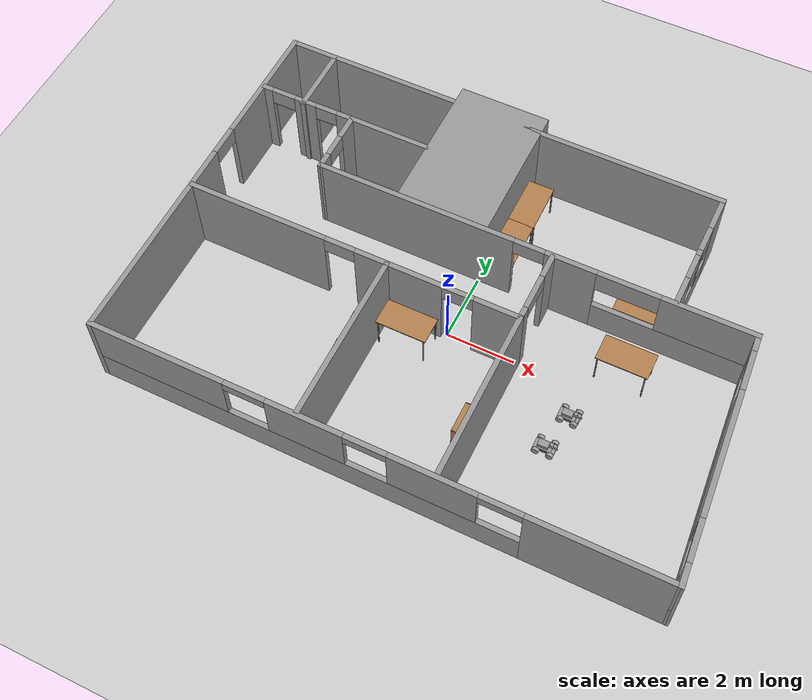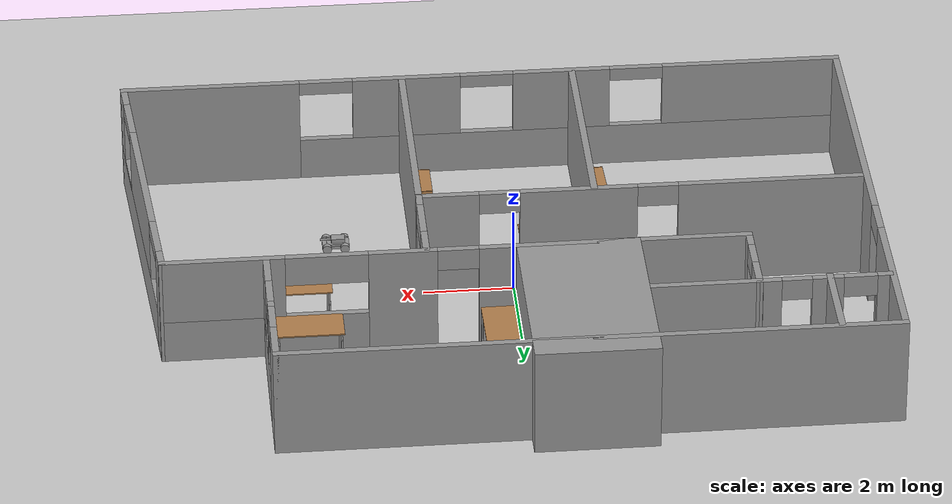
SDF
<sdf version="1.6">
 <world name="default">
  <plugin name="hello" filename="libhello.so"/>
  <light name="sun" type="directional">
   <pose>0 0 10 0 -0 0</pose>
   <diffuse>0.8 0.8 0.8 1</diffuse>
   <specular>0.2 0.2 0.2 1</specular>
   <attenuation>
    <range>1000</range>
    <constant>0.9</constant>
    <linear>0.01</linear>
    <quadratic>0.001</quadratic>
   </attenuation>
   <direction>-0.5 0.1 -0.9</direction>
  </light>
  <model name="ground_plane">
   <static>1</static>
   <link name="link">
    <collision name="collision">
     <geometry><plane><normal>0 0 1</normal><size>100 100</size></plane></geometry>
     <surface>
      <contact><collide_bitmask>65535</collide_bitmask></contact>
      <friction><ode><mu>100</mu><mu2>50</mu2></ode></friction>
     </surface>
    </collision>
    <visual name="visual">
     <cast_shadows>0</cast_shadows>
     <geometry><plane><normal>0 0 1</normal><size>100 100</size></plane></geometry>
     <material>
      <script><uri>file://media/materials/scripts/gazebo.material</uri><name>Gazebo/Grey</name></script>
     </material>
    </visual>
   </link>
  </model>
  <gravity>0 0 -9.8</gravity>
  <magnetic_field>6e-06 2.3e-05 -4.2e-05</magnetic_field>
  <atmosphere type="adiabatic"/>
  <physics name="default_physics" default="0" type="ode">
   <max_step_size>0.001</max_step_size>
   <real_time_factor>1</real_time_factor>
   <real_time_update_rate>1000</real_time_update_rate>
  </physics>
  <scene><ambient>0.4 0.4 0.4 1</ambient><background>0.7 0.7 0.7 1</background><shadows>1</shadows></scene>
  <spherical_coordinates>
   <surface_model>EARTH_WGS84</surface_model>
   <latitude_deg>0</latitude_deg>
   <longitude_deg>0</longitude_deg>
   <elevation>0</elevation>
   <heading_deg>0</heading_deg>
  </spherical_coordinates>
  <model name="Building">
   <pose>0.27526 0.57552 0 0 -0 0</pose>
   <link name="Wall_100">
    <collision name="Wall_100_Collision">
     <geometry><box><size>4.3 2.7 2.5</size></box></geometry>
     <pose>0 0 1.25 0 -0 0</pose>
    </collision>
    <visual name="Wall_100_Visual">
     <pose>0 0 1.25 0 -0 0</pose>
     <geometry><box><size>4.3 2.7 2.5</size></box></geometry>
     <material>
      <script><uri>file://media/materials/scripts/gazebo.material</uri><name>Gazebo/Grey</name></script>
      <ambient>1 1 1 1</ambient>
     </material>
     <meta><layer>0</layer></meta>
    </visual>
    <pose>-1.48764 3.58577 0 0 0 -1.5708</pose>
   </link>
   <link name="Wall_40">
    <pose>-8.07936 -0.23025 0 0 0 -1.5708</pose>
    <visual name="Wall_40_Visual_0">
     <pose>-3.61824 0 1.25 0 -0 0</pose>
     <geometry><box><size>3.76351 0.15 2.5</size></box></geometry>
     <material>
      <script><uri>file://media/materials/scripts/gazebo.material</uri><name>Gazebo/Grey</name></script>
      <ambient>1 1 1 1</ambient>
     </material>
     <meta><layer>0</layer></meta>
    </visual>
    <collision name="Wall_40_Collision_0">
     <geometry><box><size>3.76351 0.15 2.5</size></box></geometry>
     <pose>-3.61824 0 1.25 0 -0 0</pose>
    </collision>
    <visual name="Wall_40_Visual_1">
     <pose>2.33175 0 1.25 0 -0 0</pose>
     <geometry><box><size>6.33649 0.15 2.5</size></box></geometry>
     <material>
      <script><uri>file://media/materials/scripts/gazebo.material</uri><name>Gazebo/Grey</name></script>
      <ambient>1 1 1 1</ambient>
     </material>
     <meta><layer>0</layer></meta>
    </visual>
    <collision name="Wall_40_Collision_1">
     <geometry><box><size>6.33649 0.15 2.5</size></box></geometry>
     <pose>2.33175 0 1.25 0 -0 0</pose>
    </collision>
    <visual name="Wall_40_Visual_2">
     <pose>-1.28649 0 2.25 0 -0 0</pose>
     <geometry><box><size>0.9 0.15 0.5</size></box></geometry>
     <material>
      <script><uri>file://media/materials/scripts/gazebo.material</uri><name>Gazebo/Grey</name></script>
      <ambient>1 1 1 1</ambient>
     </material>
     <meta><layer>0</layer></meta>
    </visual>
    <collision name="Wall_40_Collision_2">
     <geometry><box><size>0.9 0.15 0.5</size></box></geometry>
     <pose>-1.28649 0 2.25 0 -0 0</pose>
    </collision>
   </link>
   <link name="Wall_47">
    <collision name="Wall_47_Collision">
     <geometry><box><size>13.5 0.15 2.5</size></box></geometry>
     <pose>0 0 1.25 0 -0 0</pose>
    </collision>
    <visual name="Wall_47_Visual">
     <pose>0 0 1.25 0 -0 0</pose>
     <geometry><box><size>13.5 0.15 2.5</size></box></geometry>
     <material>
      <script><uri>file://media/materials/scripts/gazebo.material</uri><name>Gazebo/Grey</name></script>
      <ambient>1 1 1 1</ambient>
     </material>
     <meta><layer>0</layer></meta>
    </visual>
    <pose>-1.40436 5.19475 0 0 -0 0</pose>
   </link>
   <link name="Wall_49">
    <pose>5.27064 3.39475 0 0 0 -1.5708</pose>
    <visual name="Wall_49_Visual_0">
     <pose>-1.33629 0 1.25 0 -0 0</pose>
     <geometry><box><size>1.07742 0.15 2.5</size></box></geometry>
     <material>
      <script><uri>file://media/materials/scripts/gazebo.material</uri><name>Gazebo/Grey</name></script>
      <ambient>1 1 1 1</ambient>
     </material>
     <meta><layer>0</layer></meta>
    </visual>
    <collision name="Wall_49_Collision_0">
     <geometry><box><size>1.07742 0.15 2.5</size></box></geometry>
     <pose>-1.33629 0 1.25 0 -0 0</pose>
    </collision>
    <visual name="Wall_49_Visual_1">
     <pose>0.538709 0 0.5 0 -0 0</pose>
     <geometry><box><size>2.67258 0.15 1</size></box></geometry>
     <material>
      <script><uri>file://media/materials/scripts/gazebo.material</uri><name>Gazebo/Grey</name></script>
      <ambient>1 1 1 1</ambient>
     </material>
     <meta><layer>0</layer></meta>
    </visual>
    <collision name="Wall_49_Collision_1">
     <geometry><box><size>2.67258 0.15 1</size></box></geometry>
     <pose>0.538709 0 0.5 0 -0 0</pose>
    </collision>
    <visual name="Wall_49_Visual_2">
     <pose>0.097651 0 1.75 0 -0 0</pose>
     <geometry><box><size>0.190465 0.15 1.5</size></box></geometry>
     <material>
      <script><uri>file://media/materials/scripts/gazebo.material</uri><name>Gazebo/Grey</name></script>
      <ambient>1 1 1 1</ambient>
     </material>
     <meta><layer>0</layer></meta>
    </visual>
    <collision name="Wall_49_Collision_2">
     <geometry><box><size>0.190465 0.15 1.5</size></box></geometry>
     <pose>0.097651 0 1.75 0 -0 0</pose>
    </collision>
    <visual name="Wall_49_Visual_3">
     <pose>1.43394 0 1.75 0 -0 0</pose>
     <geometry><box><size>0.882117 0.15 1.5</size></box></geometry>
     <material>
      <script><uri>file://media/materials/scripts/gazebo.material</uri><name>Gazebo/Grey</name></script>
      <ambient>1 1 1 1</ambient>
     </material>
     <meta><layer>0</layer></meta>
    </visual>
    <collision name="Wall_49_Collision_3">
     <geometry><box><size>0.882117 0.15 1.5</size></box></geometry>
     <pose>1.43394 0 1.75 0 -0 0</pose>
    </collision>
    <visual name="Wall_49_Visual_4">
     <pose>-0.397582 0 2.15 0 -0 0</pose>
     <geometry><box><size>0.8 0.15 0.7</size></box></geometry>
     <material>
      <script><uri>file://media/materials/scripts/gazebo.material</uri><name>Gazebo/Grey</name></script>
      <ambient>1 1 1 1</ambient>
     </material>
     <meta><layer>0</layer></meta>
    </visual>
    <collision name="Wall_49_Collision_4">
     <geometry><box><size>0.8 0.15 0.7</size></box></geometry>
     <pose>-0.397582 0 2.15 0 -0 0</pose>
    </collision>
    <visual name="Wall_49_Visual_5">
     <pose>0.592883 0 2.15 0 -0 0</pose>
     <geometry><box><size>0.8 0.15 0.7</size></box></geometry>
     <material>
      <script><uri>file://media/materials/scripts/gazebo.material</uri><name>Gazebo/Grey</name></script>
      <ambient>1 1 1 1</ambient>
     </material>
     <meta><layer>0</layer></meta>
    </visual>
    <collision name="Wall_49_Collision_5">
     <geometry><box><size>0.8 0.15 0.7</size></box></geometry>
     <pose>0.592883 0 2.15 0 -0 0</pose>
    </collision>
   </link>
   <link name="Wall_54">
    <pose>-0.002761 -5.65525 0 0 -0 3.14159</pose>
    <visual name="Wall_54_Visual_0">
     <pose>-6.13829 0 1.25 0 -0 0</pose>
     <geometry><box><size>4.02662 0.15 2.5</size></box></geometry>
     <material>
      <script><uri>file://media/materials/scripts/gazebo.material</uri><name>Gazebo/Grey</name></script>
      <ambient>1 1 1 1</ambient>
     </material>
     <meta><layer>0</layer></meta>
    </visual>
    <collision name="Wall_54_Collision_0">
     <geometry><box><size>4.02662 0.15 2.5</size></box></geometry>
     <pose>-6.13829 0 1.25 0 -0 0</pose>
    </collision>
    <visual name="Wall_54_Visual_1">
     <pose>2.01331 0 0.5 0 -0 0</pose>
     <geometry><box><size>12.2766 0.15 1</size></box></geometry>
     <material>
      <script><uri>file://media/materials/scripts/gazebo.material</uri><name>Gazebo/Grey</name></script>
      <ambient>1 1 1 1</ambient>
     </material>
     <meta><layer>0</layer></meta>
    </visual>
    <collision name="Wall_54_Collision_1">
     <geometry><box><size>12.2766 0.15 1</size></box></geometry>
     <pose>2.01331 0 0.5 0 -0 0</pose>
    </collision>
    <visual name="Wall_54_Visual_2">
     <pose>-1.70444 0 1.75 0 -0 0</pose>
     <geometry><box><size>2.44108 0.15 1.5</size></box></geometry>
     <material>
      <script><uri>file://media/materials/scripts/gazebo.material</uri><name>Gazebo/Grey</name></script>
      <ambient>1 1 1 1</ambient>
     </material>
     <meta><layer>0</layer></meta>
    </visual>
    <collision name="Wall_54_Collision_2">
     <geometry><box><size>2.44108 0.15 1.5</size></box></geometry>
     <pose>-1.70444 0 1.75 0 -0 0</pose>
    </collision>
    <visual name="Wall_54_Visual_3">
     <pose>1.81519 0 1.75 0 -0 0</pose>
     <geometry><box><size>2.19819 0.15 1.5</size></box></geometry>
     <material>
      <script><uri>file://media/materials/scripts/gazebo.material</uri><name>Gazebo/Grey</name></script>
      <ambient>1 1 1 1</ambient>
     </material>
     <meta><layer>0</layer></meta>
    </visual>
    <collision name="Wall_54_Collision_3">
     <geometry><box><size>2.19819 0.15 1.5</size></box></geometry>
     <pose>1.81519 0 1.75 0 -0 0</pose>
    </collision>
    <visual name="Wall_54_Visual_4">
     <pose>6.13294 0 1.75 0 -0 0</pose>
     <geometry><box><size>4.03732 0.15 1.5</size></box></geometry>
     <material>
      <script><uri>file://media/materials/scripts/gazebo.material</uri><name>Gazebo/Grey</name></script>
      <ambient>1 1 1 1</ambient>
     </material>
     <meta><layer>0</layer></meta>
    </visual>
    <collision name="Wall_54_Collision_4">
     <geometry><box><size>4.03732 0.15 1.5</size></box></geometry>
     <pose>6.13294 0 1.75 0 -0 0</pose>
    </collision>
    <visual name="Wall_54_Visual_5">
     <pose>-3.52498 0 2.35 0 -0 0</pose>
     <geometry><box><size>1.2 0.15 0.3</size></box></geometry>
     <material>
      <script><uri>file://media/materials/scripts/gazebo.material</uri><name>Gazebo/Grey</name></script>
      <ambient>1 1 1 1</ambient>
     </material>
     <meta><layer>0</layer></meta>
    </visual>
    <collision name="Wall_54_Collision_5">
     <geometry><box><size>1.2 0.15 0.3</size></box></geometry>
     <pose>-3.52498 0 2.35 0 -0 0</pose>
    </collision>
    <visual name="Wall_54_Visual_6">
     <pose>0.116097 0 2.35 0 -0 0</pose>
     <geometry><box><size>1.2 0.15 0.3</size></box></geometry>
     <material>
      <script><uri>file://media/materials/scripts/gazebo.material</uri><name>Gazebo/Grey</name></script>
      <ambient>1 1 1 1</ambient>
     </material>
     <meta><layer>0</layer></meta>
    </visual>
    <collision name="Wall_54_Collision_6">
     <geometry><box><size>1.2 0.15 0.3</size></box></geometry>
     <pose>0.116097 0 2.35 0 -0 0</pose>
    </collision>
    <visual name="Wall_54_Visual_7">
     <pose>3.51428 0 2.35 0 -0 0</pose>
     <geometry><box><size>1.2 0.15 0.3</size></box></geometry>
     <material>
      <script><uri>file://media/materials/scripts/gazebo.material</uri><name>Gazebo/Grey</name></script>
      <ambient>1 1 1 1</ambient>
     </material>
     <meta><layer>0</layer></meta>
    </visual>
    <collision name="Wall_54_Collision_7">
     <geometry><box><size>1.2 0.15 0.3</size></box></geometry>
     <pose>3.51428 0 2.35 0 -0 0</pose>
    </collision>
   </link>
   <link name="Wall_62">
    <pose>-6.60165 3.32498 0 0 0 -3.13189</pose>
    <visual name="Wall_62_Visual_0">
     <pose>-1.20265 0 1.25 0 -0 0</pose>
     <geometry><box><size>0.553995 0.15 2.5</size></box></geometry>
     <material>
      <script><uri>file://media/materials/scripts/gazebo.material</uri><name>Gazebo/Grey</name></script>
      <ambient>1 1 1 1</ambient>
     </material>
     <meta><layer>0</layer></meta>
    </visual>
    <collision name="Wall_62_Collision_0">
     <geometry><box><size>0.553995 0.15 2.5</size></box></geometry>
     <pose>-1.20265 0 1.25 0 -0 0</pose>
    </collision>
    <visual name="Wall_62_Visual_1">
     <pose>0.073898 0 1.25 0 -0 0</pose>
     <geometry><box><size>0.684821 0.15 2.5</size></box></geometry>
     <material>
      <script><uri>file://media/materials/scripts/gazebo.material</uri><name>Gazebo/Grey</name></script>
      <ambient>1 1 1 1</ambient>
     </material>
     <meta><layer>0</layer></meta>
    </visual>
    <collision name="Wall_62_Collision_1">
     <geometry><box><size>0.684821 0.15 2.5</size></box></geometry>
     <pose>0.073898 0 1.25 0 -0 0</pose>
    </collision>
    <visual name="Wall_62_Visual_2">
     <pose>1.31124 0 1.25 0 -0 0</pose>
     <geometry><box><size>0.336811 0.15 2.5</size></box></geometry>
     <material>
      <script><uri>file://media/materials/scripts/gazebo.material</uri><name>Gazebo/Grey</name></script>
      <ambient>1 1 1 1</ambient>
     </material>
     <meta><layer>0</layer></meta>
    </visual>
    <collision name="Wall_62_Collision_2">
     <geometry><box><size>0.336811 0.15 2.5</size></box></geometry>
     <pose>1.31124 0 1.25 0 -0 0</pose>
    </collision>
    <visual name="Wall_62_Visual_3">
     <pose>-0.597083 0 2.25 0 -0 0</pose>
     <geometry><box><size>0.65714 0.15 0.5</size></box></geometry>
     <material>
      <script><uri>file://media/materials/scripts/gazebo.material</uri><name>Gazebo/Grey</name></script>
      <ambient>1 1 1 1</ambient>
     </material>
     <meta><layer>0</layer></meta>
    </visual>
    <collision name="Wall_62_Collision_3">
     <geometry><box><size>0.65714 0.15 0.5</size></box></geometry>
     <pose>-0.597083 0 2.25 0 -0 0</pose>
    </collision>
    <visual name="Wall_62_Visual_4">
     <pose>0.779572 0 2.25 0 -0 0</pose>
     <geometry><box><size>0.726529 0.15 0.5</size></box></geometry>
     <material>
      <script><uri>file://media/materials/scripts/gazebo.material</uri><name>Gazebo/Grey</name></script>
      <ambient>1 1 1 1</ambient>
     </material>
     <meta><layer>0</layer></meta>
    </visual>
    <collision name="Wall_62_Collision_4">
     <geometry><box><size>0.726529 0.15 0.5</size></box></geometry>
     <pose>0.779572 0 2.25 0 -0 0</pose>
    </collision>
   </link>
   <link name="Wall_65">
    <pose>-5.19707 2.41361 0 0 0 -1.5708</pose>
    <visual name="Wall_65_Visual_0">
     <pose>-0.598058 0 1.25 0 -0 0</pose>
     <geometry><box><size>0.803885 0.15 2.5</size></box></geometry>
     <material>
      <script><uri>file://media/materials/scripts/gazebo.material</uri><name>Gazebo/Grey</name></script>
      <ambient>1 1 1 1</ambient>
     </material>
     <meta><layer>0</layer></meta>
    </visual>
    <collision name="Wall_65_Collision_0">
     <geometry><box><size>0.803885 0.15 2.5</size></box></geometry>
     <pose>-0.598058 0 1.25 0 -0 0</pose>
    </collision>
    <visual name="Wall_65_Visual_1">
     <pose>0.747855 0 1.25 0 -0 0</pose>
     <geometry><box><size>0.504291 0.15 2.5</size></box></geometry>
     <material>
      <script><uri>file://media/materials/scripts/gazebo.material</uri><name>Gazebo/Grey</name></script>
      <ambient>1 1 1 1</ambient>
     </material>
     <meta><layer>0</layer></meta>
    </visual>
    <collision name="Wall_65_Collision_1">
     <geometry><box><size>0.504291 0.15 2.5</size></box></geometry>
     <pose>0.747855 0 1.25 0 -0 0</pose>
    </collision>
    <visual name="Wall_65_Visual_2">
     <pose>0.149797 0 2.25 0 -0 0</pose>
     <geometry><box><size>0.691825 0.15 0.5</size></box></geometry>
     <material>
      <script><uri>file://media/materials/scripts/gazebo.material</uri><name>Gazebo/Grey</name></script>
      <ambient>1 1 1 1</ambient>
     </material>
     <meta><layer>0</layer></meta>
    </visual>
    <collision name="Wall_65_Collision_2">
     <geometry><box><size>0.691825 0.15 0.5</size></box></geometry>
     <pose>0.149797 0 2.25 0 -0 0</pose>
    </collision>
   </link>
   <link name="Wall_70">
    <pose>7.7983 -2.06765 0 0 0 -1.49414</pose>
    <visual name="Wall_70_Visual_0">
     <pose>-3.39164 0 1.25 0 -0 0</pose>
     <geometry><box><size>0.563048 0.15 2.5</size></box></geometry>
     <material>
      <script><uri>file://media/materials/scripts/gazebo.material</uri><name>Gazebo/Grey</name></script>
      <ambient>1 1 1 1</ambient>
     </material>
     <meta><layer>0</layer></meta>
    </visual>
    <collision name="Wall_70_Collision_0">
     <geometry><box><size>0.563048 0.15 2.5</size></box></geometry>
     <pose>-3.39164 0 1.25 0 -0 0</pose>
    </collision>
    <visual name="Wall_70_Visual_1">
     <pose>0.281524 0 0.5 0 -0 0</pose>
     <geometry><box><size>6.78329 0.15 1</size></box></geometry>
     <material>
      <script><uri>file://media/materials/scripts/gazebo.material</uri><name>Gazebo/Grey</name></script>
      <ambient>1 1 1 1</ambient>
     </material>
     <meta><layer>0</layer></meta>
    </visual>
    <collision name="Wall_70_Collision_1">
     <geometry><box><size>6.78329 0.15 1</size></box></geometry>
     <pose>0.281524 0 0.5 0 -0 0</pose>
    </collision>
    <visual name="Wall_70_Visual_2">
     <pose>-0.058851 0 1.75 0 -0 0</pose>
     <geometry><box><size>3.70254 0.15 1.5</size></box></geometry>
     <material>
      <script><uri>file://media/materials/scripts/gazebo.material</uri><name>Gazebo/Grey</name></script>
      <ambient>1 1 1 1</ambient>
     </material>
     <meta><layer>0</layer></meta>
    </visual>
    <collision name="Wall_70_Collision_2">
     <geometry><box><size>3.70254 0.15 1.5</size></box></geometry>
     <pose>-0.058851 0 1.75 0 -0 0</pose>
    </collision>
    <visual name="Wall_70_Visual_3">
     <pose>3.33279 0 1.75 0 -0 0</pose>
     <geometry><box><size>0.68075 0.15 1.5</size></box></geometry>
     <material>
      <script><uri>file://media/materials/scripts/gazebo.material</uri><name>Gazebo/Grey</name></script>
      <ambient>1 1 1 1</ambient>
     </material>
     <meta><layer>0</layer></meta>
    </visual>
    <collision name="Wall_70_Collision_3">
     <geometry><box><size>0.68075 0.15 1.5</size></box></geometry>
     <pose>3.33279 0 1.75 0 -0 0</pose>
    </collision>
    <visual name="Wall_70_Visual_4">
     <pose>2.39242 0 1 0 -0 0</pose>
     <geometry><box><size>1.2 0.15 0.1</size></box></geometry>
     <material>
      <script><uri>file://media/materials/scripts/gazebo.material</uri><name>Gazebo/Grey</name></script>
      <ambient>1 1 1 1</ambient>
     </material>
     <meta><layer>0</layer></meta>
    </visual>
    <collision name="Wall_70_Collision_4">
     <geometry><box><size>1.2 0.15 0.1</size></box></geometry>
     <pose>2.39242 0 1 0 -0 0</pose>
    </collision>
    <visual name="Wall_70_Visual_5">
     <pose>-2.51012 0 2.35 0 -0 0</pose>
     <geometry><box><size>1.2 0.15 0.3</size></box></geometry>
     <material>
      <script><uri>file://media/materials/scripts/gazebo.material</uri><name>Gazebo/Grey</name></script>
      <ambient>1 1 1 1</ambient>
     </material>
     <meta><layer>0</layer></meta>
    </visual>
    <collision name="Wall_70_Collision_5">
     <geometry><box><size>1.2 0.15 0.3</size></box></geometry>
     <pose>-2.51012 0 2.35 0 -0 0</pose>
    </collision>
    <visual name="Wall_70_Visual_6">
     <pose>2.39242 0 2.35 0 -0 0</pose>
     <geometry><box><size>1.2 0.15 0.3</size></box></geometry>
     <material>
      <script><uri>file://media/materials/scripts/gazebo.material</uri><name>Gazebo/Grey</name></script>
      <ambient>1 1 1 1</ambient>
     </material>
     <meta><layer>0</layer></meta>
    </visual>
    <collision name="Wall_70_Collision_6">
     <geometry><box><size>1.2 0.15 0.3</size></box></geometry>
     <pose>2.39242 0 2.35 0 -0 0</pose>
    </collision>
   </link>
   <link name="Wall_74">
    <pose>-3.11721 -0.654815 0 0 -0 0</pose>
    <visual name="Wall_74_Visual_0">
     <pose>-2.8962 0 1.25 0 -0 0</pose>
     <geometry><box><size>4.2076 0.15 2.5</size></box></geometry>
     <material>
      <script><uri>file://media/materials/scripts/gazebo.material</uri><name>Gazebo/Grey</name></script>
      <ambient>1 1 1 1</ambient>
     </material>
     <meta><layer>0</layer></meta>
    </visual>
    <collision name="Wall_74_Collision_0">
     <geometry><box><size>4.2076 0.15 2.5</size></box></geometry>
     <pose>-2.8962 0 1.25 0 -0 0</pose>
    </collision>
    <visual name="Wall_74_Visual_1">
     <pose>1.40494 0 1.25 0 -0 0</pose>
     <geometry><box><size>2.59468 0.15 2.5</size></box></geometry>
     <material>
      <script><uri>file://media/materials/scripts/gazebo.material</uri><name>Gazebo/Grey</name></script>
      <ambient>1 1 1 1</ambient>
     </material>
     <meta><layer>0</layer></meta>
    </visual>
    <collision name="Wall_74_Collision_1">
     <geometry><box><size>2.59468 0.15 2.5</size></box></geometry>
     <pose>1.40494 0 1.25 0 -0 0</pose>
    </collision>
    <visual name="Wall_74_Visual_2">
     <pose>4.30114 0 1.25 0 -0 0</pose>
     <geometry><box><size>1.39772 0.15 2.5</size></box></geometry>
     <material>
      <script><uri>file://media/materials/scripts/gazebo.material</uri><name>Gazebo/Grey</name></script>
      <ambient>1 1 1 1</ambient>
     </material>
     <meta><layer>0</layer></meta>
    </visual>
    <collision name="Wall_74_Collision_2">
     <geometry><box><size>1.39772 0.15 2.5</size></box></geometry>
     <pose>4.30114 0 1.25 0 -0 0</pose>
    </collision>
    <visual name="Wall_74_Visual_3">
     <pose>-0.342396 0 2.25 0 -0 0</pose>
     <geometry><box><size>0.9 0.15 0.5</size></box></geometry>
     <material>
      <script><uri>file://media/materials/scripts/gazebo.material</uri><name>Gazebo/Grey</name></script>
      <ambient>1 1 1 1</ambient>
     </material>
     <meta><layer>0</layer></meta>
    </visual>
    <collision name="Wall_74_Collision_3">
     <geometry><box><size>0.9 0.15 0.5</size></box></geometry>
     <pose>-0.342396 0 2.25 0 -0 0</pose>
    </collision>
    <visual name="Wall_74_Visual_4">
     <pose>3.15228 0 2.25 0 -0 0</pose>
     <geometry><box><size>0.9 0.15 0.5</size></box></geometry>
     <material>
      <script><uri>file://media/materials/scripts/gazebo.material</uri><name>Gazebo/Grey</name></script>
      <ambient>1 1 1 1</ambient>
     </material>
     <meta><layer>0</layer></meta>
    </visual>
    <collision name="Wall_74_Collision_4">
     <geometry><box><size>0.9 0.15 0.5</size></box></geometry>
     <pose>3.15228 0 2.25 0 -0 0</pose>
    </collision>
   </link>
   <link name="Wall_75">
    <collision name="Wall_75_Collision">
     <geometry><box><size>5 0.15 2.5</size></box></geometry>
     <pose>0 0 1.25 0 -0 0</pose>
    </collision>
    <visual name="Wall_75_Visual">
     <pose>0 0 1.25 0 -0 0</pose>
     <geometry><box><size>5 0.15 2.5</size></box></geometry>
     <material>
      <script><uri>file://media/materials/scripts/gazebo.material</uri><name>Gazebo/Grey</name></script>
      <ambient>1 1 1 1</ambient>
     </material>
     <meta><layer>0</layer></meta>
    </visual>
    <pose>1.80779 -3.07981 0 0 0 -1.5708</pose>
   </link>
   <link name="Wall_79">
    <collision name="Wall_79_Collision">
     <geometry><box><size>5 0.15 2.5</size></box></geometry>
     <pose>0 0 1.25 0 -0 0</pose>
    </collision>
    <visual name="Wall_79_Visual">
     <pose>0 0 1.25 0 -0 0</pose>
     <geometry><box><size>5 0.15 2.5</size></box></geometry>
     <material>
      <script><uri>file://media/materials/scripts/gazebo.material</uri><name>Gazebo/Grey</name></script>
      <ambient>1 1 1 1</ambient>
     </material>
     <meta><layer>0</layer></meta>
    </visual>
    <pose>-2.05138 -3.12608 0 0 0 -1.5708</pose>
   </link>
   <link name="Wall_83">
    <collision name="Wall_83_Collision">
     <geometry><box><size>2 0.15 2.5</size></box></geometry>
     <pose>0 0 1.25 0 -0 0</pose>
    </collision>
    <visual name="Wall_83_Visual">
     <pose>0 0 1.25 0 -0 0</pose>
     <geometry><box><size>2 0.15 2.5</size></box></geometry>
     <material>
      <script><uri>file://media/materials/scripts/gazebo.material</uri><name>Gazebo/Grey</name></script>
      <ambient>1 1 1 1</ambient>
     </material>
     <meta><layer>0</layer></meta>
    </visual>
    <pose>-6.72313 4.20134 0 0 0 -1.5708</pose>
   </link>
   <link name="Wall_85">
    <collision name="Wall_85_Collision">
     <geometry><box><size>2.5 0.15 2.5</size></box></geometry>
     <pose>0 0 1.25 0 -0 0</pose>
    </collision>
    <visual name="Wall_85_Visual">
     <pose>0 0 1.25 0 -0 0</pose>
     <geometry><box><size>2.5 0.15 2.5</size></box></geometry>
     <material>
      <script><uri>file://media/materials/scripts/gazebo.material</uri><name>Gazebo/Grey</name></script>
      <ambient>1 1 1 1</ambient>
     </material>
     <meta><layer>0</layer></meta>
    </visual>
    <pose>-4.02207 3.33861 0 0 -0 0</pose>
   </link>
   <link name="Wall_89">
    <pose>1.80779 0.395185 0 0 -0 1.5708</pose>
    <visual name="Wall_89_Visual_0">
     <pose>-0.9132 0 1.25 0 -0 0</pose>
     <geometry><box><size>0.423601 0.15 2.5</size></box></geometry>
     <material>
      <script><uri>file://media/materials/scripts/gazebo.material</uri><name>Gazebo/Grey</name></script>
      <ambient>1 1 1 1</ambient>
     </material>
     <meta><layer>0</layer></meta>
    </visual>
    <collision name="Wall_89_Collision_0">
     <geometry><box><size>0.423601 0.15 2.5</size></box></geometry>
     <pose>-0.9132 0 1.25 0 -0 0</pose>
    </collision>
    <visual name="Wall_89_Visual_1">
     <pose>0.749251 0 1.25 0 -0 0</pose>
     <geometry><box><size>0.751499 0.15 2.5</size></box></geometry>
     <material>
      <script><uri>file://media/materials/scripts/gazebo.material</uri><name>Gazebo/Grey</name></script>
      <ambient>1 1 1 1</ambient>
     </material>
     <meta><layer>0</layer></meta>
    </visual>
    <collision name="Wall_89_Collision_1">
     <geometry><box><size>0.751499 0.15 2.5</size></box></geometry>
     <pose>0.749251 0 1.25 0 -0 0</pose>
    </collision>
    <visual name="Wall_89_Visual_2">
     <pose>-0.163949 0 2.25 0 -0 0</pose>
     <geometry><box><size>1.0749 0.15 0.5</size></box></geometry>
     <material>
      <script><uri>file://media/materials/scripts/gazebo.material</uri><name>Gazebo/Grey</name></script>
      <ambient>1 1 1 1</ambient>
     </material>
     <meta><layer>0</layer></meta>
    </visual>
    <collision name="Wall_89_Collision_2">
     <geometry><box><size>1.0749 0.15 0.5</size></box></geometry>
     <pose>-0.163949 0 2.25 0 -0 0</pose>
    </collision>
   </link>
   <link name="Wall_97">
    <pose>1.16285 1.50428 0 0 -0 0.002464</pose>
    <visual name="Wall_97_Visual_0">
     <pose>-3.46225 0 1.25 0 -0 0</pose>
     <geometry><box><size>5.94536 0.15 2.5</size></box></geometry>
     <material>
      <script><uri>file://media/materials/scripts/gazebo.material</uri><name>Gazebo/Grey</name></script>
      <ambient>1 1 1 1</ambient>
     </material>
     <meta><layer>0</layer></meta>
    </visual>
    <collision name="Wall_97_Collision_0">
     <geometry><box><size>5.94536 0.15 2.5</size></box></geometry>
     <pose>-3.46225 0 1.25 0 -0 0</pose>
    </collision>
    <visual name="Wall_97_Visual_1">
     <pose>1.15705 0 1.25 0 -0 0</pose>
     <geometry><box><size>1.49323 0.15 2.5</size></box></geometry>
     <material>
      <script><uri>file://media/materials/scripts/gazebo.material</uri><name>Gazebo/Grey</name></script>
      <ambient>1 1 1 1</ambient>
     </material>
     <meta><layer>0</layer></meta>
    </visual>
    <collision name="Wall_97_Collision_1">
     <geometry><box><size>1.49323 0.15 2.5</size></box></geometry>
     <pose>1.15705 0 1.25 0 -0 0</pose>
    </collision>
    <visual name="Wall_97_Visual_2">
     <pose>4.1693 0 0.5 0 -0 0</pose>
     <geometry><box><size>4.53127 0.15 1</size></box></geometry>
     <material>
      <script><uri>file://media/materials/scripts/gazebo.material</uri><name>Gazebo/Grey</name></script>
      <ambient>1 1 1 1</ambient>
     </material>
     <meta><layer>0</layer></meta>
    </visual>
    <collision name="Wall_97_Collision_2">
     <geometry><box><size>4.53127 0.15 1</size></box></geometry>
     <pose>4.1693 0 0.5 0 -0 0</pose>
    </collision>
    <visual name="Wall_97_Visual_3">
     <pose>5.0693 0 1.75 0 -0 0</pose>
     <geometry><box><size>2.73128 0.15 1.5</size></box></geometry>
     <material>
      <script><uri>file://media/materials/scripts/gazebo.material</uri><name>Gazebo/Grey</name></script>
      <ambient>1 1 1 1</ambient>
     </material>
     <meta><layer>0</layer></meta>
    </visual>
    <collision name="Wall_97_Collision_3">
     <geometry><box><size>2.73128 0.15 1.5</size></box></geometry>
     <pose>5.0693 0 1.75 0 -0 0</pose>
    </collision>
    <visual name="Wall_97_Visual_4">
     <pose>2.80366 0 2.15 0 -0 0</pose>
     <geometry><box><size>1.8 0.15 0.7</size></box></geometry>
     <material>
      <script><uri>file://media/materials/scripts/gazebo.material</uri><name>Gazebo/Grey</name></script>
      <ambient>1 1 1 1</ambient>
     </material>
     <meta><layer>0</layer></meta>
    </visual>
    <collision name="Wall_97_Collision_4">
     <geometry><box><size>1.8 0.15 0.7</size></box></geometry>
     <pose>2.80366 0 2.15 0 -0 0</pose>
    </collision>
    <visual name="Wall_97_Visual_5">
     <pose>-0.039569 0 2.25 0 -0 0</pose>
     <geometry><box><size>0.9 0.15 0.5</size></box></geometry>
     <material>
      <script><uri>file://media/materials/scripts/gazebo.material</uri><name>Gazebo/Grey</name></script>
      <ambient>1 1 1 1</ambient>
     </material>
     <meta><layer>0</layer></meta>
    </visual>
    <collision name="Wall_97_Collision_5">
     <geometry><box><size>0.9 0.15 0.5</size></box></geometry>
     <pose>-0.039569 0 2.25 0 -0 0</pose>
    </collision>
   </link>
   <static>1</static>
  </model>
  <model name="bookshelf">
   <static>1</static>
   <link name="link">
    <inertial><mass>1</mass></inertial>
    <collision name="back">
     <pose>0 0.005 0.6 0 -0 0</pose>
     <geometry><box><size>0.9 0.01 1.2</size></box></geometry>
    </collision>
    <visual name="visual1">
     <pose>0 0.005 0.6 0 -0 0</pose>
     <geometry><box><size>0.9 0.01 1.2</size></box></geometry>
     <material>
      <script><uri>file://media/materials/scripts/gazebo.material</uri><name>Gazebo/Wood</name></script>
     </material>
    </visual>
    <collision name="left_side">
     <pose>0.45 -0.195 0.6 0 -0 0</pose>
     <geometry><box><size>0.02 0.4 1.2</size></box></geometry>
    </collision>
    <visual name="visual2">
     <pose>0.45 -0.195 0.6 0 -0 0</pose>
     <geometry><box><size>0.02 0.4 1.2</size></box></geometry>
     <material>
      <script><uri>file://media/materials/scripts/gazebo.material</uri><name>Gazebo/Wood</name></script>
     </material>
    </visual>
    <collision name="right_side">
     <pose>-0.45 -0.195 0.6 0 -0 0</pose>
     <geometry><box><size>0.02 0.4 1.2</size></box></geometry>
    </collision>
    <visual name="visual3">
     <pose>-0.45 -0.195 0.6 0 -0 0</pose>
     <geometry><box><size>0.02 0.4 1.2</size></box></geometry>
     <material>
      <script><uri>file://media/materials/scripts/gazebo.material</uri><name>Gazebo/Wood</name></script>
     </material>
    </visual>
    <collision name="bottom">
     <pose>0 -0.195 0.03 0 -0 0</pose>
     <geometry><box><size>0.88 0.4 0.06</size></box></geometry>
    </collision>
    <visual name="visual4">
     <pose>0 -0.195 0.03 0 -0 0</pose>
     <geometry><box><size>0.88 0.4 0.06</size></box></geometry>
     <material>
      <script><uri>file://media/materials/scripts/gazebo.material</uri><name>Gazebo/Wood</name></script>
     </material>
    </visual>
    <collision name="top">
     <pose>0 -0.195 1.19 0 -0 0</pose>
     <geometry><box><size>0.88 0.4 0.02</size></box></geometry>
    </collision>
    <visual name="visual5">
     <pose>0 -0.195 1.19 0 -0 0</pose>
     <geometry><box><size>0.88 0.4 0.02</size></box></geometry>
     <material>
      <script><uri>file://media/materials/scripts/gazebo.material</uri><name>Gazebo/Wood</name></script>
     </material>
    </visual>
    <collision name="low_shelf">
     <pose>0 -0.195 0.43 0 -0 0</pose>
     <geometry><box><size>0.88 0.4 0.02</size></box></geometry>
    </collision>
    <visual name="visual6">
     <pose>0 -0.195 0.43 0 -0 0</pose>
     <geometry><box><size>0.88 0.4 0.02</size></box></geometry>
     <material>
      <script><uri>file://media/materials/scripts/gazebo.material</uri><name>Gazebo/Wood</name></script>
     </material>
    </visual>
    <collision name="high_shelf">
     <pose>0 -0.195 0.8 0 -0 0</pose>
     <geometry><box><size>0.88 0.4 0.02</size></box></geometry>
    </collision>
    <visual name="visual7">
     <pose>0 -0.195 0.8 0 -0 0</pose>
     <geometry><box><size>0.88 0.4 0.02</size></box></geometry>
     <material>
      <script><uri>file://media/materials/scripts/gazebo.material</uri><name>Gazebo/Wood</name></script>
     </material>
    </visual>
   </link>
   <pose>2.00246 -2.74716 0 0 0 -1.57238</pose>
  </model>
  <model name="table">
   <static>1</static>
   <link name="link">
    <collision name="surface">
     <pose>0 0 1 0 -0 0</pose>
     <geometry><box><size>1.5 0.8 0.03</size></box></geometry>
     <surface><friction><ode><mu>0.6</mu><mu2>0.6</mu2></ode></friction></surface>
    </collision>
    <visual name="visual1">
     <pose>0 0 1 0 -0 0</pose>
     <geometry><box><size>1.5 0.8 0.03</size></box></geometry>
     <material>
      <script><uri>file://media/materials/scripts/gazebo.material</uri><name>Gazebo/Wood</name></script>
     </material>
    </visual>
    <collision name="front_left_leg">
     <pose>0.68 0.38 0.5 0 -0 0</pose>
     <geometry><cylinder><radius>0.02</radius><length>1</length></cylinder></geometry>
    </collision>
    <visual name="front_left_leg">
     <pose>0.68 0.38 0.5 0 -0 0</pose>
     <geometry><cylinder><radius>0.02</radius><length>1</length></cylinder></geometry>
     <material>
      <script><uri>file://media/materials/scripts/gazebo.material</uri><name>Gazebo/Grey</name></script>
     </material>
    </visual>
    <collision name="front_right_leg">
     <pose>0.68 -0.38 0.5 0 -0 0</pose>
     <geometry><cylinder><radius>0.02</radius><length>1</length></cylinder></geometry>
    </collision>
    <visual name="front_right_leg">
     <pose>0.68 -0.38 0.5 0 -0 0</pose>
     <geometry><cylinder><radius>0.02</radius><length>1</length></cylinder></geometry>
     <material>
      <script><uri>file://media/materials/scripts/gazebo.material</uri><name>Gazebo/Grey</name></script>
     </material>
    </visual>
    <collision name="back_right_leg">
     <pose>-0.68 -0.38 0.5 0 -0 0</pose>
     <geometry><cylinder><radius>0.02</radius><length>1</length></cylinder></geometry>
    </collision>
    <visual name="back_right_leg">
     <pose>-0.68 -0.38 0.5 0 -0 0</pose>
     <geometry><cylinder><radius>0.02</radius><length>1</length></cylinder></geometry>
     <material>
      <script><uri>file://media/materials/scripts/gazebo.material</uri><name>Gazebo/Grey</name></script>
     </material>
    </visual>
    <collision name="back_left_leg">
     <pose>-0.68 0.38 0.5 0 -0 0</pose>
     <geometry><cylinder><radius>0.02</radius><length>1</length></cylinder></geometry>
    </collision>
    <visual name="back_left_leg">
     <pose>-0.68 0.38 0.5 0 -0 0</pose>
     <geometry><cylinder><radius>0.02</radius><length>1</length></cylinder></geometry>
     <material>
      <script><uri>file://media/materials/scripts/gazebo.material</uri><name>Gazebo/Grey</name></script>
     </material>
    </visual>
   </link>
   <pose>4.82678 0.914784 0 0 -0 0</pose>
  </model>
  <model name="table_0">
   <static>1</static>
   <link name="link">
    <collision name="surface">
     <pose>0 0 1 0 -0 0</pose>
     <geometry><box><size>1.5 0.8 0.03</size></box></geometry>
     <surface><friction><ode><mu>0.6</mu><mu2>0.6</mu2></ode></friction></surface>
    </collision>
    <visual name="visual1">
     <pose>0 0 1 0 -0 0</pose>
     <geometry><box><size>1.5 0.8 0.03</size></box></geometry>
     <material>
      <script><uri>file://media/materials/scripts/gazebo.material</uri><name>Gazebo/Wood</name></script>
     </material>
    </visual>
    <collision name="front_left_leg">
     <pose>0.68 0.38 0.5 0 -0 0</pose>
     <geometry><cylinder><radius>0.02</radius><length>1</length></cylinder></geometry>
    </collision>
    <visual name="front_left_leg">
     <pose>0.68 0.38 0.5 0 -0 0</pose>
     <geometry><cylinder><radius>0.02</radius><length>1</length></cylinder></geometry>
     <material>
      <script><uri>file://media/materials/scripts/gazebo.material</uri><name>Gazebo/Grey</name></script>
     </material>
    </visual>
    <collision name="front_right_leg">
     <pose>0.68 -0.38 0.5 0 -0 0</pose>
     <geometry><cylinder><radius>0.02</radius><length>1</length></cylinder></geometry>
    </collision>
    <visual name="front_right_leg">
     <pose>0.68 -0.38 0.5 0 -0 0</pose>
     <geometry><cylinder><radius>0.02</radius><length>1</length></cylinder></geometry>
     <material>
      <script><uri>file://media/materials/scripts/gazebo.material</uri><name>Gazebo/Grey</name></script>
     </material>
    </visual>
    <collision name="back_right_leg">
     <pose>-0.68 -0.38 0.5 0 -0 0</pose>
     <geometry><cylinder><radius>0.02</radius><length>1</length></cylinder></geometry>
    </collision>
    <visual name="back_right_leg">
     <pose>-0.68 -0.38 0.5 0 -0 0</pose>
     <geometry><cylinder><radius>0.02</radius><length>1</length></cylinder></geometry>
     <material>
      <script><uri>file://media/materials/scripts/gazebo.material</uri><name>Gazebo/Grey</name></script>
     </material>
    </visual>
    <collision name="back_left_leg">
     <pose>-0.68 0.38 0.5 0 -0 0</pose>
     <geometry><cylinder><radius>0.02</radius><length>1</length></cylinder></geometry>
    </collision>
    <visual name="back_left_leg">
     <pose>-0.68 0.38 0.5 0 -0 0</pose>
     <geometry><cylinder><radius>0.02</radius><length>1</length></cylinder></geometry>
     <material>
      <script><uri>file://media/materials/scripts/gazebo.material</uri><name>Gazebo/Grey</name></script>
     </material>
    </visual>
   </link>
   <pose>-0.933659 -0.643381 0 0 -0 0</pose>
  </model>
  <model name="table_1">
   <static>1</static>
   <link name="link">
    <collision name="surface">
     <pose>0 0 1 0 -0 0</pose>
     <geometry><box><size>1.5 0.8 0.03</size></box></geometry>
     <surface><friction><ode><mu>0.6</mu><mu2>0.6</mu2></ode></friction></surface>
    </collision>
    <visual name="visual1">
     <pose>0 0 1 0 -0 0</pose>
     <geometry><box><size>1.5 0.8 0.03</size></box></geometry>
     <material>
      <script><uri>file://media/materials/scripts/gazebo.material</uri><name>Gazebo/Wood</name></script>
     </material>
    </visual>
    <collision name="front_left_leg">
     <pose>0.68 0.38 0.5 0 -0 0</pose>
     <geometry><cylinder><radius>0.02</radius><length>1</length></cylinder></geometry>
    </collision>
    <visual name="front_left_leg">
     <pose>0.68 0.38 0.5 0 -0 0</pose>
     <geometry><cylinder><radius>0.02</radius><length>1</length></cylinder></geometry>
     <material>
      <script><uri>file://media/materials/scripts/gazebo.material</uri><name>Gazebo/Grey</name></script>
     </material>
    </visual>
    <collision name="front_right_leg">
     <pose>0.68 -0.38 0.5 0 -0 0</pose>
     <geometry><cylinder><radius>0.02</radius><length>1</length></cylinder></geometry>
    </collision>
    <visual name="front_right_leg">
     <pose>0.68 -0.38 0.5 0 -0 0</pose>
     <geometry><cylinder><radius>0.02</radius><length>1</length></cylinder></geometry>
     <material>
      <script><uri>file://media/materials/scripts/gazebo.material</uri><name>Gazebo/Grey</name></script>
     </material>
    </visual>
    <collision name="back_right_leg">
     <pose>-0.68 -0.38 0.5 0 -0 0</pose>
     <geometry><cylinder><radius>0.02</radius><length>1</length></cylinder></geometry>
    </collision>
    <visual name="back_right_leg">
     <pose>-0.68 -0.38 0.5 0 -0 0</pose>
     <geometry><cylinder><radius>0.02</radius><length>1</length></cylinder></geometry>
     <material>
      <script><uri>file://media/materials/scripts/gazebo.material</uri><name>Gazebo/Grey</name></script>
     </material>
    </visual>
    <collision name="back_left_leg">
     <pose>-0.68 0.38 0.5 0 -0 0</pose>
     <geometry><cylinder><radius>0.02</radius><length>1</length></cylinder></geometry>
    </collision>
    <visual name="back_left_leg">
     <pose>-0.68 0.38 0.5 0 -0 0</pose>
     <geometry><cylinder><radius>0.02</radius><length>1</length></cylinder></geometry>
     <material>
      <script><uri>file://media/materials/scripts/gazebo.material</uri><name>Gazebo/Grey</name></script>
     </material>
    </visual>
   </link>
   <pose>4.67032 2.55949 0 0 -0 0</pose>
  </model>
  <model name="table_2">
   <static>1</static>
   <link name="link">
    <collision name="surface">
     <pose>0 0 1 0 -0 0</pose>
     <geometry><box><size>1.5 0.8 0.03</size></box></geometry>
     <surface><friction><ode><mu>0.6</mu><mu2>0.6</mu2></ode></friction></surface>
    </collision>
    <visual name="visual1">
     <pose>0 0 1 0 -0 0</pose>
     <geometry><box><size>1.5 0.8 0.03</size></box></geometry>
     <material>
      <script><uri>file://media/materials/scripts/gazebo.material</uri><name>Gazebo/Wood</name></script>
     </material>
    </visual>
    <collision name="front_left_leg">
     <pose>0.68 0.38 0.5 0 -0 0</pose>
     <geometry><cylinder><radius>0.02</radius><length>1</length></cylinder></geometry>
    </collision>
    <visual name="front_left_leg">
     <pose>0.68 0.38 0.5 0 -0 0</pose>
     <geometry><cylinder><radius>0.02</radius><length>1</length></cylinder></geometry>
     <material>
      <script><uri>file://media/materials/scripts/gazebo.material</uri><name>Gazebo/Grey</name></script>
     </material>
    </visual>
    <collision name="front_right_leg">
     <pose>0.68 -0.38 0.5 0 -0 0</pose>
     <geometry><cylinder><radius>0.02</radius><length>1</length></cylinder></geometry>
    </collision>
    <visual name="front_right_leg">
     <pose>0.68 -0.38 0.5 0 -0 0</pose>
     <geometry><cylinder><radius>0.02</radius><length>1</length></cylinder></geometry>
     <material>
      <script><uri>file://media/materials/scripts/gazebo.material</uri><name>Gazebo/Grey</name></script>
     </material>
    </visual>
    <collision name="back_right_leg">
     <pose>-0.68 -0.38 0.5 0 -0 0</pose>
     <geometry><cylinder><radius>0.02</radius><length>1</length></cylinder></geometry>
    </collision>
    <visual name="back_right_leg">
     <pose>-0.68 -0.38 0.5 0 -0 0</pose>
     <geometry><cylinder><radius>0.02</radius><length>1</length></cylinder></geometry>
     <material>
      <script><uri>file://media/materials/scripts/gazebo.material</uri><name>Gazebo/Grey</name></script>
     </material>
    </visual>
    <collision name="back_left_leg">
     <pose>-0.68 0.38 0.5 0 -0 0</pose>
     <geometry><cylinder><radius>0.02</radius><length>1</length></cylinder></geometry>
    </collision>
    <visual name="back_left_leg">
     <pose>-0.68 0.38 0.5 0 -0 0</pose>
     <geometry><cylinder><radius>0.02</radius><length>1</length></cylinder></geometry>
     <material>
      <script><uri>file://media/materials/scripts/gazebo.material</uri><name>Gazebo/Grey</name></script>
     </material>
    </visual>
   </link>
   <pose>0.509065 2.93824 0 0 0 -1.56281</pose>
  </model>
  <model name="table_2_clone">
   <static>1</static>
   <link name="link">
    <collision name="surface">
     <pose>0 0 1 0 -0 0</pose>
     <geometry><box><size>1.5 0.8 0.03</size></box></geometry>
     <surface><friction><ode><mu>0.6</mu><mu2>0.6</mu2></ode></friction></surface>
    </collision>
    <visual name="visual1">
     <pose>0 0 1 0 -0 0</pose>
     <geometry><box><size>1.5 0.8 0.03</size></box></geometry>
     <material>
      <script><uri>file://media/materials/scripts/gazebo.material</uri><name>Gazebo/Wood</name></script>
     </material>
    </visual>
    <collision name="front_left_leg">
     <pose>0.68 0.38 0.5 0 -0 0</pose>
     <geometry><cylinder><radius>0.02</radius><length>1</length></cylinder></geometry>
    </collision>
    <visual name="front_left_leg">
     <pose>0.68 0.38 0.5 0 -0 0</pose>
     <geometry><cylinder><radius>0.02</radius><length>1</length></cylinder></geometry>
     <material>
      <script><uri>file://media/materials/scripts/gazebo.material</uri><name>Gazebo/Grey</name></script>
     </material>
    </visual>
    <collision name="front_right_leg">
     <pose>0.68 -0.38 0.5 0 -0 0</pose>
     <geometry><cylinder><radius>0.02</radius><length>1</length></cylinder></geometry>
    </collision>
    <visual name="front_right_leg">
     <pose>0.68 -0.38 0.5 0 -0 0</pose>
     <geometry><cylinder><radius>0.02</radius><length>1</length></cylinder></geometry>
     <material>
      <script><uri>file://media/materials/scripts/gazebo.material</uri><name>Gazebo/Grey</name></script>
     </material>
    </visual>
    <collision name="back_right_leg">
     <pose>-0.68 -0.38 0.5 0 -0 0</pose>
     <geometry><cylinder><radius>0.02</radius><length>1</length></cylinder></geometry>
    </collision>
    <visual name="back_right_leg">
     <pose>-0.68 -0.38 0.5 0 -0 0</pose>
     <geometry><cylinder><radius>0.02</radius><length>1</length></cylinder></geometry>
     <material>
      <script><uri>file://media/materials/scripts/gazebo.material</uri><name>Gazebo/Grey</name></script>
     </material>
    </visual>
    <collision name="back_left_leg">
     <pose>-0.68 0.38 0.5 0 -0 0</pose>
     <geometry><cylinder><radius>0.02</radius><length>1</length></cylinder></geometry>
    </collision>
    <visual name="back_left_leg">
     <pose>-0.68 0.38 0.5 0 -0 0</pose>
     <geometry><cylinder><radius>0.02</radius><length>1</length></cylinder></geometry>
     <material>
      <script><uri>file://media/materials/scripts/gazebo.material</uri><name>Gazebo/Grey</name></script>
     </material>
    </visual>
   </link>
   <pose>0.511822 4.42523 0 0 0 -1.56281</pose>
  </model>
  <model name="bookshelf_0">
   <static>1</static>
   <link name="link">
    <inertial><mass>1</mass></inertial>
    <collision name="back">
     <pose>0 0.005 0.6 0 -0 0</pose>
     <geometry><box><size>0.9 0.01 1.2</size></box></geometry>
    </collision>
    <visual name="visual1">
     <pose>0 0.005 0.6 0 -0 0</pose>
     <geometry><box><size>0.9 0.01 1.2</size></box></geometry>
     <material>
      <script><uri>file://media/materials/scripts/gazebo.material</uri><name>Gazebo/Wood</name></script>
     </material>
    </visual>
    <collision name="left_side">
     <pose>0.45 -0.195 0.6 0 -0 0</pose>
     <geometry><box><size>0.02 0.4 1.2</size></box></geometry>
    </collision>
    <visual name="visual2">
     <pose>0.45 -0.195 0.6 0 -0 0</pose>
     <geometry><box><size>0.02 0.4 1.2</size></box></geometry>
     <material>
      <script><uri>file://media/materials/scripts/gazebo.material</uri><name>Gazebo/Wood</name></script>
     </material>
    </visual>
    <collision name="right_side">
     <pose>-0.45 -0.195 0.6 0 -0 0</pose>
     <geometry><box><size>0.02 0.4 1.2</size></box></geometry>
    </collision>
    <visual name="visual3">
     <pose>-0.45 -0.195 0.6 0 -0 0</pose>
     <geometry><box><size>0.02 0.4 1.2</size></box></geometry>
     <material>
      <script><uri>file://media/materials/scripts/gazebo.material</uri><name>Gazebo/Wood</name></script>
     </material>
    </visual>
    <collision name="bottom">
     <pose>0 -0.195 0.03 0 -0 0</pose>
     <geometry><box><size>0.88 0.4 0.06</size></box></geometry>
    </collision>
    <visual name="visual4">
     <pose>0 -0.195 0.03 0 -0 0</pose>
     <geometry><box><size>0.88 0.4 0.06</size></box></geometry>
     <material>
      <script><uri>file://media/materials/scripts/gazebo.material</uri><name>Gazebo/Wood</name></script>
     </material>
    </visual>
    <collision name="top">
     <pose>0 -0.195 1.19 0 -0 0</pose>
     <geometry><box><size>0.88 0.4 0.02</size></box></geometry>
    </collision>
    <visual name="visual5">
     <pose>0 -0.195 1.19 0 -0 0</pose>
     <geometry><box><size>0.88 0.4 0.02</size></box></geometry>
     <material>
      <script><uri>file://media/materials/scripts/gazebo.material</uri><name>Gazebo/Wood</name></script>
     </material>
    </visual>
    <collision name="low_shelf">
     <pose>0 -0.195 0.43 0 -0 0</pose>
     <geometry><box><size>0.88 0.4 0.02</size></box></geometry>
    </collision>
    <visual name="visual6">
     <pose>0 -0.195 0.43 0 -0 0</pose>
     <geometry><box><size>0.88 0.4 0.02</size></box></geometry>
     <material>
      <script><uri>file://media/materials/scripts/gazebo.material</uri><name>Gazebo/Wood</name></script>
     </material>
    </visual>
    <collision name="high_shelf">
     <pose>0 -0.195 0.8 0 -0 0</pose>
     <geometry><box><size>0.88 0.4 0.02</size></box></geometry>
    </collision>
    <visual name="visual7">
     <pose>0 -0.195 0.8 0 -0 0</pose>
     <geometry><box><size>0.88 0.4 0.02</size></box></geometry>
     <material>
      <script><uri>file://media/materials/scripts/gazebo.material</uri><name>Gazebo/Wood</name></script>
     </material>
    </visual>
   </link>
   <pose>-1.89229 -0.61162 0 0 0 -1.53942</pose>
  </model>
  <model name="bookshelf_0_clone">
   <static>1</static>
   <link name="link">
    <inertial><mass>1</mass></inertial>
    <collision name="back">
     <pose>0 0.005 0.6 0 -0 0</pose>
     <geometry><box><size>0.9 0.01 1.2</size></box></geometry>
    </collision>
    <visual name="visual1">
     <pose>0 0.005 0.6 0 -0 0</pose>
     <geometry><box><size>0.9 0.01 1.2</size></box></geometry>
     <material>
      <script><uri>file://media/materials/scripts/gazebo.material</uri><name>Gazebo/Wood</name></script>
     </material>
    </visual>
    <collision name="left_side">
     <pose>0.45 -0.195 0.6 0 -0 0</pose>
     <geometry><box><size>0.02 0.4 1.2</size></box></geometry>
    </collision>
    <visual name="visual2">
     <pose>0.45 -0.195 0.6 0 -0 0</pose>
     <geometry><box><size>0.02 0.4 1.2</size></box></geometry>
     <material>
      <script><uri>file://media/materials/scripts/gazebo.material</uri><name>Gazebo/Wood</name></script>
     </material>
    </visual>
    <collision name="right_side">
     <pose>-0.45 -0.195 0.6 0 -0 0</pose>
     <geometry><box><size>0.02 0.4 1.2</size></box></geometry>
    </collision>
    <visual name="visual3">
     <pose>-0.45 -0.195 0.6 0 -0 0</pose>
     <geometry><box><size>0.02 0.4 1.2</size></box></geometry>
     <material>
      <script><uri>file://media/materials/scripts/gazebo.material</uri><name>Gazebo/Wood</name></script>
     </material>
    </visual>
    <collision name="bottom">
     <pose>0 -0.195 0.03 0 -0 0</pose>
     <geometry><box><size>0.88 0.4 0.06</size></box></geometry>
    </collision>
    <visual name="visual4">
     <pose>0 -0.195 0.03 0 -0 0</pose>
     <geometry><box><size>0.88 0.4 0.06</size></box></geometry>
     <material>
      <script><uri>file://media/materials/scripts/gazebo.material</uri><name>Gazebo/Wood</name></script>
     </material>
    </visual>
    <collision name="top">
     <pose>0 -0.195 1.19 0 -0 0</pose>
     <geometry><box><size>0.88 0.4 0.02</size></box></geometry>
    </collision>
    <visual name="visual5">
     <pose>0 -0.195 1.19 0 -0 0</pose>
     <geometry><box><size>0.88 0.4 0.02</size></box></geometry>
     <material>
      <script><uri>file://media/materials/scripts/gazebo.material</uri><name>Gazebo/Wood</name></script>
     </material>
    </visual>
    <collision name="low_shelf">
     <pose>0 -0.195 0.43 0 -0 0</pose>
     <geometry><box><size>0.88 0.4 0.02</size></box></geometry>
    </collision>
    <visual name="visual6">
     <pose>0 -0.195 0.43 0 -0 0</pose>
     <geometry><box><size>0.88 0.4 0.02</size></box></geometry>
     <material>
      <script><uri>file://media/materials/scripts/gazebo.material</uri><name>Gazebo/Wood</name></script>
     </material>
    </visual>
    <collision name="high_shelf">
     <pose>0 -0.195 0.8 0 -0 0</pose>
     <geometry><box><size>0.88 0.4 0.02</size></box></geometry>
    </collision>
    <visual name="visual7">
     <pose>0 -0.195 0.8 0 -0 0</pose>
     <geometry><box><size>0.88 0.4 0.02</size></box></geometry>
     <material>
      <script><uri>file://media/materials/scripts/gazebo.material</uri><name>Gazebo/Wood</name></script>
     </material>
    </visual>
   </link>
   <pose>-1.88638 -1.55332 0 0 0 -1.53942</pose>
  </model>
  <model name="bookshelf_0_clone_0">
   <static>1</static>
   <link name="link">
    <inertial><mass>1</mass></inertial>
    <collision name="back">
     <pose>0 0.005 0.6 0 -0 0</pose>
     <geometry><box><size>0.9 0.01 1.2</size></box></geometry>
    </collision>
    <visual name="visual1">
     <pose>0 0.005 0.6 0 -0 0</pose>
     <geometry><box><size>0.9 0.01 1.2</size></box></geometry>
     <material>
      <script><uri>file://media/materials/scripts/gazebo.material</uri><name>Gazebo/Wood</name></script>
     </material>
    </visual>
    <collision name="left_side">
     <pose>0.45 -0.195 0.6 0 -0 0</pose>
     <geometry><box><size>0.02 0.4 1.2</size></box></geometry>
    </collision>
    <visual name="visual2">
     <pose>0.45 -0.195 0.6 0 -0 0</pose>
     <geometry><box><size>0.02 0.4 1.2</size></box></geometry>
     <material>
      <script><uri>file://media/materials/scripts/gazebo.material</uri><name>Gazebo/Wood</name></script>
     </material>
    </visual>
    <collision name="right_side">
     <pose>-0.45 -0.195 0.6 0 -0 0</pose>
     <geometry><box><size>0.02 0.4 1.2</size></box></geometry>
    </collision>
    <visual name="visual3">
     <pose>-0.45 -0.195 0.6 0 -0 0</pose>
     <geometry><box><size>0.02 0.4 1.2</size></box></geometry>
     <material>
      <script><uri>file://media/materials/scripts/gazebo.material</uri><name>Gazebo/Wood</name></script>
     </material>
    </visual>
    <collision name="bottom">
     <pose>0 -0.195 0.03 0 -0 0</pose>
     <geometry><box><size>0.88 0.4 0.06</size></box></geometry>
    </collision>
    <visual name="visual4">
     <pose>0 -0.195 0.03 0 -0 0</pose>
     <geometry><box><size>0.88 0.4 0.06</size></box></geometry>
     <material>
      <script><uri>file://media/materials/scripts/gazebo.material</uri><name>Gazebo/Wood</name></script>
     </material>
    </visual>
    <collision name="top">
     <pose>0 -0.195 1.19 0 -0 0</pose>
     <geometry><box><size>0.88 0.4 0.02</size></box></geometry>
    </collision>
    <visual name="visual5">
     <pose>0 -0.195 1.19 0 -0 0</pose>
     <geometry><box><size>0.88 0.4 0.02</size></box></geometry>
     <material>
      <script><uri>file://media/materials/scripts/gazebo.material</uri><name>Gazebo/Wood</name></script>
     </material>
    </visual>
    <collision name="low_shelf">
     <pose>0 -0.195 0.43 0 -0 0</pose>
     <geometry><box><size>0.88 0.4 0.02</size></box></geometry>
    </collision>
    <visual name="visual6">
     <pose>0 -0.195 0.43 0 -0 0</pose>
     <geometry><box><size>0.88 0.4 0.02</size></box></geometry>
     <material>
      <script><uri>file://media/materials/scripts/gazebo.material</uri><name>Gazebo/Wood</name></script>
     </material>
    </visual>
    <collision name="high_shelf">
     <pose>0 -0.195 0.8 0 -0 0</pose>
     <geometry><box><size>0.88 0.4 0.02</size></box></geometry>
    </collision>
    <visual name="visual7">
     <pose>0 -0.195 0.8 0 -0 0</pose>
     <geometry><box><size>0.88 0.4 0.02</size></box></geometry>
     <material>
      <script><uri>file://media/materials/scripts/gazebo.material</uri><name>Gazebo/Wood</name></script>
     </material>
    </visual>
   </link>
   <pose>-1.88893 -2.49325 0 0 0 -1.53942</pose>
  </model>
  <model name="TankBot">
   <link name="link_0">
    <pose>4.02291 -0.912872 0.464375 0 -0 0</pose>
    <inertial>
     <mass>1</mass>
     <inertia>
      <ixx>0.166667</ixx>
      <ixy>0</ixy>
      <ixz>0</ixz>
      <iyy>0.166667</iyy>
      <iyz>0</iyz>
      <izz>0.166667</izz>
     </inertia>
    </inertial>
    <visual name="visual">
     <geometry><box><size>0.6 0.3 0.1</size></box></geometry>
     <material>
      <lighting>1</lighting>
      <script><uri>file://media/materials/scripts/gazebo.material</uri><name>Gazebo/Grey</name></script>
      <shader type="pixel"><normal_map>__default__</normal_map></shader>
      <ambient>0.3 0.3 0.3 1</ambient>
      <diffuse>0.7 0.7 0.7 1</diffuse>
      <specular>0.01 0.01 0.01 1</specular>
      <emissive>0 0 0 1</emissive>
     </material>
    </visual>
    <collision name="collision">
     <geometry><box><size>0.6 0.3 0.1</size></box></geometry>
     <surface>
      <friction>
       <ode><mu>1</mu><mu2>1</mu2><fdir1>0 0 0</fdir1><slip1>0</slip1><slip2>0</slip2></ode>
       <torsional>
        <coefficient>1</coefficient>
        <patch_radius>0</patch_radius>
        <surface_radius>0</surface_radius>
        <use_patch_radius>1</use_patch_radius>
        <ode><slip>0</slip></ode>
       </torsional>
      </friction>
      <bounce><restitution_coefficient>0</restitution_coefficient><threshold>1e+06</threshold></bounce>
      <contact>
       <collide_without_contact>0</collide_without_contact>
       <collide_without_contact_bitmask>1</collide_without_contact_bitmask>
       <collide_bitmask>1</collide_bitmask>
       <ode>
        <soft_cfm>0</soft_cfm>
        <soft_erp>0.2</soft_erp>
        <kp>1e+13</kp>
        <kd>1</kd>
        <max_vel>0.01</max_vel>
        <min_depth>0</min_depth>
       </ode>
       <bullet>
        <split_impulse>1</split_impulse>
        <split_impulse_penetration_threshold>-0.01</split_impulse_penetration_threshold>
        <soft_cfm>0</soft_cfm>
        <soft_erp>0.2</soft_erp>
        <kp>1e+13</kp>
        <kd>1</kd>
       </bullet>
      </contact>
     </surface>
    </collision>
   </link>
   <link name="link_1_clone">
    <pose>3.82291 -1.11288 0.464375 1.5707 -0 0</pose>
    <inertial>
     <mass>1</mass>
     <inertia><ixx>0.145833</ixx><ixy>0</ixy><ixz>0</ixz><iyy>0.145833</iyy><iyz>0</iyz><izz>0.125</izz></inertia>
    </inertial>
    <visual name="visual">
     <geometry><cylinder><radius>0.1</radius><length>0.1</length></cylinder></geometry>
     <material>
      <lighting>1</lighting>
      <script><uri>file://media/materials/scripts/gazebo.material</uri><name>Gazebo/Grey</name></script>
      <shader type="pixel"><normal_map>__default__</normal_map></shader>
      <ambient>0.3 0.3 0.3 1</ambient>
      <diffuse>0.7 0.7 0.7 1</diffuse>
      <specular>0.01 0.01 0.01 1</specular>
      <emissive>0 0 0 1</emissive>
     </material>
    </visual>
    <collision name="collision">
     <geometry><cylinder><radius>0.1</radius><length>0.1</length></cylinder></geometry>
     <surface>
      <friction>
       <ode><mu>1</mu><mu2>1</mu2><fdir1>0 0 0</fdir1><slip1>0</slip1><slip2>0</slip2></ode>
       <torsional>
        <coefficient>1</coefficient>
        <patch_radius>0</patch_radius>
        <surface_radius>0</surface_radius>
        <use_patch_radius>1</use_patch_radius>
        <ode><slip>0</slip></ode>
       </torsional>
      </friction>
      <bounce><restitution_coefficient>0</restitution_coefficient><threshold>1e+06</threshold></bounce>
      <contact>
       <collide_without_contact>0</collide_without_contact>
       <collide_without_contact_bitmask>1</collide_without_contact_bitmask>
       <collide_bitmask>1</collide_bitmask>
       <ode>
        <soft_cfm>0</soft_cfm>
        <soft_erp>0.2</soft_erp>
        <kp>1e+13</kp>
        <kd>1</kd>
        <max_vel>0.01</max_vel>
        <min_depth>0</min_depth>
       </ode>
       <bullet>
        <split_impulse>1</split_impulse>
        <split_impulse_penetration_threshold>-0.01</split_impulse_penetration_threshold>
        <soft_cfm>0</soft_cfm>
        <soft_erp>0.2</soft_erp>
        <kp>1e+13</kp>
        <kd>1</kd>
       </bullet>
      </contact>
     </surface>
    </collision>
   </link>
   <link name="link_1_clone_0">
    <pose>4.22291 -1.11288 0.464375 1.5707 -0 0</pose>
    <inertial>
     <mass>1</mass>
     <inertia><ixx>0.145833</ixx><ixy>0</ixy><ixz>0</ixz><iyy>0.145833</iyy><iyz>0</iyz><izz>0.125</izz></inertia>
    </inertial>
    <visual name="visual">
     <geometry><cylinder><radius>0.1</radius><length>0.1</length></cylinder></geometry>
     <material>
      <lighting>1</lighting>
      <script><uri>file://media/materials/scripts/gazebo.material</uri><name>Gazebo/Grey</name></script>
      <shader type="pixel"><normal_map>__default__</normal_map></shader>
      <ambient>0.3 0.3 0.3 1</ambient>
      <diffuse>0.7 0.7 0.7 1</diffuse>
      <specular>0.01 0.01 0.01 1</specular>
      <emissive>0 0 0 1</emissive>
     </material>
    </visual>
    <collision name="collision">
     <geometry><cylinder><radius>0.1</radius><length>0.1</length></cylinder></geometry>
     <surface>
      <friction>
       <ode><mu>1</mu><mu2>1</mu2><fdir1>0 0 0</fdir1><slip1>0</slip1><slip2>0</slip2></ode>
       <torsional>
        <coefficient>1</coefficient>
        <patch_radius>0</patch_radius>
        <surface_radius>0</surface_radius>
        <use_patch_radius>1</use_patch_radius>
        <ode><slip>0</slip></ode>
       </torsional>
      </friction>
      <bounce><restitution_coefficient>0</restitution_coefficient><threshold>1e+06</threshold></bounce>
      <contact>
       <collide_without_contact>0</collide_without_contact>
       <collide_without_contact_bitmask>1</collide_without_contact_bitmask>
       <collide_bitmask>1</collide_bitmask>
       <ode>
        <soft_cfm>0</soft_cfm>
        <soft_erp>0.2</soft_erp>
        <kp>1e+13</kp>
        <kd>1</kd>
        <max_vel>0.01</max_vel>
        <min_depth>0</min_depth>
       </ode>
       <bullet>
        <split_impulse>1</split_impulse>
        <split_impulse_penetration_threshold>-0.01</split_impulse_penetration_threshold>
        <soft_cfm>0</soft_cfm>
        <soft_erp>0.2</soft_erp>
        <kp>1e+13</kp>
        <kd>1</kd>
       </bullet>
      </contact>
     </surface>
    </collision>
   </link>
   <link name="link_1_clone_0_clone">
    <pose>3.82291 -0.712862 0.464375 1.5707 -0 0</pose>
    <inertial>
     <mass>1</mass>
     <inertia><ixx>0.145833</ixx><ixy>0</ixy><ixz>0</ixz><iyy>0.145833</iyy><iyz>0</iyz><izz>0.125</izz></inertia>
    </inertial>
    <visual name="visual">
     <geometry><cylinder><radius>0.1</radius><length>0.1</length></cylinder></geometry>
     <material>
      <lighting>1</lighting>
      <script><uri>file://media/materials/scripts/gazebo.material</uri><name>Gazebo/Grey</name></script>
      <shader type="pixel"><normal_map>__default__</normal_map></shader>
      <ambient>0.3 0.3 0.3 1</ambient>
      <diffuse>0.7 0.7 0.7 1</diffuse>
      <specular>0.01 0.01 0.01 1</specular>
      <emissive>0 0 0 1</emissive>
     </material>
    </visual>
    <collision name="collision">
     <geometry><cylinder><radius>0.1</radius><length>0.1</length></cylinder></geometry>
     <surface>
      <friction>
       <ode><mu>1</mu><mu2>1</mu2><fdir1>0 0 0</fdir1><slip1>0</slip1><slip2>0</slip2></ode>
       <torsional>
        <coefficient>1</coefficient>
        <patch_radius>0</patch_radius>
        <surface_radius>0</surface_radius>
        <use_patch_radius>1</use_patch_radius>
        <ode><slip>0</slip></ode>
       </torsional>
      </friction>
      <bounce><restitution_coefficient>0</restitution_coefficient><threshold>1e+06</threshold></bounce>
      <contact>
       <collide_without_contact>0</collide_without_contact>
       <collide_without_contact_bitmask>1</collide_without_contact_bitmask>
       <collide_bitmask>1</collide_bitmask>
       <ode>
        <soft_cfm>0</soft_cfm>
        <soft_erp>0.2</soft_erp>
        <kp>1e+13</kp>
        <kd>1</kd>
        <max_vel>0.01</max_vel>
        <min_depth>0</min_depth>
       </ode>
       <bullet>
        <split_impulse>1</split_impulse>
        <split_impulse_penetration_threshold>-0.01</split_impulse_penetration_threshold>
        <soft_cfm>0</soft_cfm>
        <soft_erp>0.2</soft_erp>
        <kp>1e+13</kp>
        <kd>1</kd>
       </bullet>
      </contact>
     </surface>
    </collision>
   </link>
   <link name="link_1_clone_clone">
    <pose>4.22291 -0.712862 0.464375 1.5707 -0 0</pose>
    <inertial>
     <mass>1</mass>
     <inertia><ixx>0.145833</ixx><ixy>0</ixy><ixz>0</ixz><iyy>0.145833</iyy><iyz>0</iyz><izz>0.125</izz></inertia>
    </inertial>
    <visual name="visual">
     <geometry><cylinder><radius>0.1</radius><length>0.1</length></cylinder></geometry>
     <material>
      <lighting>1</lighting>
      <script><uri>file://media/materials/scripts/gazebo.material</uri><name>Gazebo/Grey</name></script>
      <shader type="pixel"><normal_map>__default__</normal_map></shader>
      <ambient>0.3 0.3 0.3 1</ambient>
      <diffuse>0.7 0.7 0.7 1</diffuse>
      <specular>0.01 0.01 0.01 1</specular>
      <emissive>0 0 0 1</emissive>
     </material>
    </visual>
    <collision name="collision">
     <geometry><cylinder><radius>0.1</radius><length>0.1</length></cylinder></geometry>
     <surface>
      <friction>
       <ode><mu>1</mu><mu2>1</mu2><fdir1>0 0 0</fdir1><slip1>0</slip1><slip2>0</slip2></ode>
       <torsional>
        <coefficient>1</coefficient>
        <patch_radius>0</patch_radius>
        <surface_radius>0</surface_radius>
        <use_patch_radius>1</use_patch_radius>
        <ode><slip>0</slip></ode>
       </torsional>
      </friction>
      <bounce><restitution_coefficient>0</restitution_coefficient><threshold>1e+06</threshold></bounce>
      <contact>
       <collide_without_contact>0</collide_without_contact>
       <collide_without_contact_bitmask>1</collide_without_contact_bitmask>
       <collide_bitmask>1</collide_bitmask>
       <ode>
        <soft_cfm>0</soft_cfm>
        <soft_erp>0.2</soft_erp>
        <kp>1e+13</kp>
        <kd>1</kd>
        <max_vel>0.01</max_vel>
        <min_depth>0</min_depth>
       </ode>
       <bullet>
        <split_impulse>1</split_impulse>
        <split_impulse_penetration_threshold>-0.01</split_impulse_penetration_threshold>
        <soft_cfm>0</soft_cfm>
        <soft_erp>0.2</soft_erp>
        <kp>1e+13</kp>
        <kd>1</kd>
       </bullet>
      </contact>
     </surface>
    </collision>
   </link>
   <link name="link_2_clone">
    <pose>4.02291 -0.912872 0.509375 0 -0 0</pose>
    <inertial>
     <mass>1</mass>
     <inertia>
      <ixx>0.166667</ixx>
      <ixy>0</ixy>
      <ixz>0</ixz>
      <iyy>0.166667</iyy>
      <iyz>0</iyz>
      <izz>0.166667</izz>
     </inertia>
    </inertial>
    <visual name="visual">
     <geometry><box><size>0.4 0.3 0.05</size></box></geometry>
     <material>
      <lighting>1</lighting>
      <script><uri>file://media/materials/scripts/gazebo.material</uri><name>Gazebo/Grey</name></script>
      <shader type="pixel"><normal_map>__default__</normal_map></shader>
      <ambient>0.3 0.3 0.3 1</ambient>
      <diffuse>0.7 0.7 0.7 1</diffuse>
      <specular>0.01 0.01 0.01 1</specular>
      <emissive>0 0 0 1</emissive>
     </material>
    </visual>
    <collision name="collision">
     <geometry><box><size>0.4 0.3 0.05</size></box></geometry>
     <surface>
      <friction>
       <ode><mu>1</mu><mu2>1</mu2><fdir1>0 0 0</fdir1><slip1>0</slip1><slip2>0</slip2></ode>
       <torsional>
        <coefficient>1</coefficient>
        <patch_radius>0</patch_radius>
        <surface_radius>0</surface_radius>
        <use_patch_radius>1</use_patch_radius>
        <ode><slip>0</slip></ode>
       </torsional>
      </friction>
      <bounce><restitution_coefficient>0</restitution_coefficient><threshold>1e+06</threshold></bounce>
      <contact>
       <collide_without_contact>0</collide_without_contact>
       <collide_without_contact_bitmask>1</collide_without_contact_bitmask>
       <collide_bitmask>1</collide_bitmask>
       <ode>
        <soft_cfm>0</soft_cfm>
        <soft_erp>0.2</soft_erp>
        <kp>1e+13</kp>
        <kd>1</kd>
        <max_vel>0.01</max_vel>
        <min_depth>0</min_depth>
       </ode>
       <bullet>
        <split_impulse>1</split_impulse>
        <split_impulse_penetration_threshold>-0.01</split_impulse_penetration_threshold>
        <soft_cfm>0</soft_cfm>
        <soft_erp>0.2</soft_erp>
        <kp>1e+13</kp>
        <kd>1</kd>
       </bullet>
      </contact>
     </surface>
    </collision>
   </link>
   <link name="link_3_clone">
    <pose>3.97291 -0.912872 0.584375 0 -0 0</pose>
    <inertial>
     <mass>1</mass>
     <inertia>
      <ixx>0.166667</ixx>
      <ixy>0</ixy>
      <ixz>0</ixz>
      <iyy>0.166667</iyy>
      <iyz>0</iyz>
      <izz>0.166667</izz>
     </inertia>
    </inertial>
    <visual name="visual">
     <geometry><box><size>0.3 0.2 0.1</size></box></geometry>
     <material>
      <lighting>1</lighting>
      <script><uri>file://media/materials/scripts/gazebo.material</uri><name>Gazebo/Grey</name></script>
      <shader type="pixel"><normal_map>__default__</normal_map></shader>
      <ambient>0.3 0.3 0.3 1</ambient>
      <diffuse>0.7 0.7 0.7 1</diffuse>
      <specular>0.01 0.01 0.01 1</specular>
      <emissive>0 0 0 1</emissive>
     </material>
    </visual>
    <collision name="collision">
     <geometry><box><size>0.3 0.2 0.1</size></box></geometry>
     <surface>
      <friction>
       <ode><mu>1</mu><mu2>1</mu2><fdir1>0 0 0</fdir1><slip1>0</slip1><slip2>0</slip2></ode>
       <torsional>
        <coefficient>1</coefficient>
        <patch_radius>0</patch_radius>
        <surface_radius>0</surface_radius>
        <use_patch_radius>1</use_patch_radius>
        <ode><slip>0</slip></ode>
       </torsional>
      </friction>
      <bounce><restitution_coefficient>0</restitution_coefficient><threshold>1e+06</threshold></bounce>
      <contact>
       <collide_without_contact>0</collide_without_contact>
       <collide_without_contact_bitmask>1</collide_without_contact_bitmask>
       <collide_bitmask>1</collide_bitmask>
       <ode>
        <soft_cfm>0</soft_cfm>
        <soft_erp>0.2</soft_erp>
        <kp>1e+13</kp>
        <kd>1</kd>
        <max_vel>0.01</max_vel>
        <min_depth>0</min_depth>
       </ode>
       <bullet>
        <split_impulse>1</split_impulse>
        <split_impulse_penetration_threshold>-0.01</split_impulse_penetration_threshold>
        <soft_cfm>0</soft_cfm>
        <soft_erp>0.2</soft_erp>
        <kp>1e+13</kp>
        <kd>1</kd>
       </bullet>
      </contact>
     </surface>
    </collision>
   </link>
   <link name="link_4_clone">
    <pose>4.24792 -0.912872 0.584375 1.5707 0 1.5707</pose>
    <inertial>
     <mass>1</mass>
     <inertia><ixx>0.145833</ixx><ixy>0</ixy><ixz>0</ixz><iyy>0.145833</iyy><iyz>0</iyz><izz>0.125</izz></inertia>
    </inertial>
    <visual name="visual">
     <geometry><cylinder><radius>0.02</radius><length>0.25</length></cylinder></geometry>
     <material>
      <lighting>1</lighting>
      <script><uri>file://media/materials/scripts/gazebo.material</uri><name>Gazebo/Grey</name></script>
      <shader type="pixel"><normal_map>__default__</normal_map></shader>
      <ambient>0.3 0.3 0.3 1</ambient>
      <diffuse>0.7 0.7 0.7 1</diffuse>
      <specular>0.01 0.01 0.01 1</specular>
      <emissive>0 0 0 1</emissive>
     </material>
    </visual>
    <collision name="collision">
     <geometry><cylinder><radius>0.02</radius><length>0.25</length></cylinder></geometry>
     <surface>
      <friction>
       <ode><mu>1</mu><mu2>1</mu2><fdir1>0 0 0</fdir1><slip1>0</slip1><slip2>0</slip2></ode>
       <torsional>
        <coefficient>1</coefficient>
        <patch_radius>0</patch_radius>
        <surface_radius>0</surface_radius>
        <use_patch_radius>1</use_patch_radius>
        <ode><slip>0</slip></ode>
       </torsional>
      </friction>
      <bounce><restitution_coefficient>0</restitution_coefficient><threshold>1e+06</threshold></bounce>
      <contact>
       <collide_without_contact>0</collide_without_contact>
       <collide_without_contact_bitmask>1</collide_without_contact_bitmask>
       <collide_bitmask>1</collide_bitmask>
       <ode>
        <soft_cfm>0</soft_cfm>
        <soft_erp>0.2</soft_erp>
        <kp>1e+13</kp>
        <kd>1</kd>
        <max_vel>0.01</max_vel>
        <min_depth>0</min_depth>
       </ode>
       <bullet>
        <split_impulse>1</split_impulse>
        <split_impulse_penetration_threshold>-0.01</split_impulse_penetration_threshold>
        <soft_cfm>0</soft_cfm>
        <soft_erp>0.2</soft_erp>
        <kp>1e+13</kp>
        <kd>1</kd>
       </bullet>
      </contact>
     </surface>
    </collision>
   </link>
   <joint name="link_0_JOINT_2" type="revolute">
    <parent>link_0</parent>
    <child>link_1_clone_clone</child>
    <axis>
     <xyz>0 0 1</xyz>
     <use_parent_model_frame>0</use_parent_model_frame>
     <limit>
      <lower>-1.79769e+308</lower>
      <upper>1.79769e+308</upper>
      <effort>-1</effort>
      <velocity>-1</velocity>
     </limit>
     <dynamics>
      <spring_reference>0</spring_reference>
      <spring_stiffness>0</spring_stiffness>
      <damping>0</damping>
     </dynamics>
    </axis>
    <physics>
     <ode><limit><cfm>0</cfm><erp>0.2</erp></limit><suspension><cfm>0</cfm><erp>0.2</erp></suspension></ode>
    </physics>
   </joint>
   <joint name="link_0_JOINT_3" type="revolute">
    <parent>link_0</parent>
    <child>link_1_clone_0</child>
    <axis>
     <xyz>0 0 1</xyz>
     <use_parent_model_frame>0</use_parent_model_frame>
     <limit>
      <lower>-1.79769e+308</lower>
      <upper>1.79769e+308</upper>
      <effort>-1</effort>
      <velocity>-1</velocity>
     </limit>
     <dynamics>
      <spring_reference>0</spring_reference>
      <spring_stiffness>0</spring_stiffness>
      <damping>0</damping>
     </dynamics>
    </axis>
    <physics>
     <ode><limit><cfm>0</cfm><erp>0.2</erp></limit><suspension><cfm>0</cfm><erp>0.2</erp></suspension></ode>
    </physics>
   </joint>
   <joint name="link_0_JOINT_4" type="revolute">
    <parent>link_0</parent>
    <child>link_1_clone_0_clone</child>
    <axis>
     <xyz>0 0 1</xyz>
     <use_parent_model_frame>0</use_parent_model_frame>
     <limit>
      <lower>-1.79769e+308</lower>
      <upper>1.79769e+308</upper>
      <effort>-1</effort>
      <velocity>-1</velocity>
     </limit>
     <dynamics>
      <spring_reference>0</spring_reference>
      <spring_stiffness>0</spring_stiffness>
      <damping>0</damping>
     </dynamics>
    </axis>
    <physics>
     <ode><limit><cfm>0</cfm><erp>0.2</erp></limit><suspension><cfm>0</cfm><erp>0.2</erp></suspension></ode>
    </physics>
   </joint>
   <joint name="link_0_JOINT_5" type="revolute">
    <parent>link_0</parent>
    <child>link_1_clone</child>
    <axis>
     <xyz>0 0 1</xyz>
     <use_parent_model_frame>0</use_parent_model_frame>
     <limit>
      <lower>-1.79769e+308</lower>
      <upper>1.79769e+308</upper>
      <effort>-1</effort>
      <velocity>-1</velocity>
     </limit>
     <dynamics>
      <spring_reference>0</spring_reference>
      <spring_stiffness>0</spring_stiffness>
      <damping>0</damping>
     </dynamics>
    </axis>
    <physics>
     <ode><limit><cfm>0</cfm><erp>0.2</erp></limit><suspension><cfm>0</cfm><erp>0.2</erp></suspension></ode>
    </physics>
   </joint>
   <joint name="link_0_JOINT_7" type="fixed">
    <parent>link_0</parent>
    <child>link_2_clone</child>
    <physics>
     <ode><limit><cfm>0</cfm><erp>0.2</erp></limit><suspension><cfm>0</cfm><erp>0.2</erp></suspension></ode>
    </physics>
   </joint>
   <joint name="link_2_clone_JOINT_9" type="fixed">
    <parent>link_2_clone</parent>
    <child>link_3_clone</child>
    <physics>
     <ode><limit><cfm>0</cfm><erp>0.2</erp></limit><suspension><cfm>0</cfm><erp>0.2</erp></suspension></ode>
    </physics>
   </joint>
   <joint name="link_3_clone_JOINT_11" type="fixed">
    <parent>link_3_clone</parent>
    <child>link_4_clone</child>
    <physics>
     <ode><limit><cfm>0</cfm><erp>0.2</erp></limit><suspension><cfm>0</cfm><erp>0.2</erp></suspension></ode>
    </physics>
   </joint>
   <static>0</static>
   <pose>0.011588 0.017541 -0.364368 -0 3e-06 -0.004814</pose>
  </model>
  <model name="TankBot_0">
   <link name="link_0">
    <pose>4.02291 -0.912872 0.464375 0 -0 0</pose>
    <inertial>
     <mass>1</mass>
     <inertia>
      <ixx>0.166667</ixx>
      <ixy>0</ixy>
      <ixz>0</ixz>
      <iyy>0.166667</iyy>
      <iyz>0</iyz>
      <izz>0.166667</izz>
     </inertia>
    </inertial>
    <visual name="visual">
     <geometry><box><size>0.6 0.3 0.1</size></box></geometry>
     <material>
      <lighting>1</lighting>
      <script><uri>file://media/materials/scripts/gazebo.material</uri><name>Gazebo/Grey</name></script>
      <shader type="pixel"><normal_map>__default__</normal_map></shader>
      <ambient>0.3 0.3 0.3 1</ambient>
      <diffuse>0.7 0.7 0.7 1</diffuse>
      <specular>0.01 0.01 0.01 1</specular>
      <emissive>0 0 0 1</emissive>
     </material>
    </visual>
    <collision name="collision">
     <geometry><box><size>0.6 0.3 0.1</size></box></geometry>
     <surface>
      <friction>
       <ode><mu>1</mu><mu2>1</mu2><fdir1>0 0 0</fdir1><slip1>0</slip1><slip2>0</slip2></ode>
       <torsional>
        <coefficient>1</coefficient>
        <patch_radius>0</patch_radius>
        <surface_radius>0</surface_radius>
        <use_patch_radius>1</use_patch_radius>
        <ode><slip>0</slip></ode>
       </torsional>
      </friction>
      <bounce><restitution_coefficient>0</restitution_coefficient><threshold>1e+06</threshold></bounce>
      <contact>
       <collide_without_contact>0</collide_without_contact>
       <collide_without_contact_bitmask>1</collide_without_contact_bitmask>
       <collide_bitmask>1</collide_bitmask>
       <ode>
        <soft_cfm>0</soft_cfm>
        <soft_erp>0.2</soft_erp>
        <kp>1e+13</kp>
        <kd>1</kd>
        <max_vel>0.01</max_vel>
        <min_depth>0</min_depth>
       </ode>
       <bullet>
        <split_impulse>1</split_impulse>
        <split_impulse_penetration_threshold>-0.01</split_impulse_penetration_threshold>
        <soft_cfm>0</soft_cfm>
        <soft_erp>0.2</soft_erp>
        <kp>1e+13</kp>
        <kd>1</kd>
       </bullet>
      </contact>
     </surface>
    </collision>
   </link>
   <link name="link_1_clone">
    <pose>3.82291 -1.11288 0.464375 1.5707 -0 0</pose>
    <inertial>
     <mass>1</mass>
     <inertia><ixx>0.145833</ixx><ixy>0</ixy><ixz>0</ixz><iyy>0.145833</iyy><iyz>0</iyz><izz>0.125</izz></inertia>
    </inertial>
    <visual name="visual">
     <geometry><cylinder><radius>0.1</radius><length>0.1</length></cylinder></geometry>
     <material>
      <lighting>1</lighting>
      <script><uri>file://media/materials/scripts/gazebo.material</uri><name>Gazebo/Grey</name></script>
      <shader type="pixel"><normal_map>__default__</normal_map></shader>
      <ambient>0.3 0.3 0.3 1</ambient>
      <diffuse>0.7 0.7 0.7 1</diffuse>
      <specular>0.01 0.01 0.01 1</specular>
      <emissive>0 0 0 1</emissive>
     </material>
    </visual>
    <collision name="collision">
     <geometry><cylinder><radius>0.1</radius><length>0.1</length></cylinder></geometry>
     <surface>
      <friction>
       <ode><mu>1</mu><mu2>1</mu2><fdir1>0 0 0</fdir1><slip1>0</slip1><slip2>0</slip2></ode>
       <torsional>
        <coefficient>1</coefficient>
        <patch_radius>0</patch_radius>
        <surface_radius>0</surface_radius>
        <use_patch_radius>1</use_patch_radius>
        <ode><slip>0</slip></ode>
       </torsional>
      </friction>
      <bounce><restitution_coefficient>0</restitution_coefficient><threshold>1e+06</threshold></bounce>
      <contact>
       <collide_without_contact>0</collide_without_contact>
       <collide_without_contact_bitmask>1</collide_without_contact_bitmask>
       <collide_bitmask>1</collide_bitmask>
       <ode>
        <soft_cfm>0</soft_cfm>
        <soft_erp>0.2</soft_erp>
        <kp>1e+13</kp>
        <kd>1</kd>
        <max_vel>0.01</max_vel>
        <min_depth>0</min_depth>
       </ode>
       <bullet>
        <split_impulse>1</split_impulse>
        <split_impulse_penetration_threshold>-0.01</split_impulse_penetration_threshold>
        <soft_cfm>0</soft_cfm>
        <soft_erp>0.2</soft_erp>
        <kp>1e+13</kp>
        <kd>1</kd>
       </bullet>
      </contact>
     </surface>
    </collision>
   </link>
   <link name="link_1_clone_0">
    <pose>4.22291 -1.11288 0.464375 1.5707 -0 0</pose>
    <inertial>
     <mass>1</mass>
     <inertia><ixx>0.145833</ixx><ixy>0</ixy><ixz>0</ixz><iyy>0.145833</iyy><iyz>0</iyz><izz>0.125</izz></inertia>
    </inertial>
    <visual name="visual">
     <geometry><cylinder><radius>0.1</radius><length>0.1</length></cylinder></geometry>
     <material>
      <lighting>1</lighting>
      <script><uri>file://media/materials/scripts/gazebo.material</uri><name>Gazebo/Grey</name></script>
      <shader type="pixel"><normal_map>__default__</normal_map></shader>
      <ambient>0.3 0.3 0.3 1</ambient>
      <diffuse>0.7 0.7 0.7 1</diffuse>
      <specular>0.01 0.01 0.01 1</specular>
      <emissive>0 0 0 1</emissive>
     </material>
    </visual>
    <collision name="collision">
     <geometry><cylinder><radius>0.1</radius><length>0.1</length></cylinder></geometry>
     <surface>
      <friction>
       <ode><mu>1</mu><mu2>1</mu2><fdir1>0 0 0</fdir1><slip1>0</slip1><slip2>0</slip2></ode>
       <torsional>
        <coefficient>1</coefficient>
        <patch_radius>0</patch_radius>
        <surface_radius>0</surface_radius>
        <use_patch_radius>1</use_patch_radius>
        <ode><slip>0</slip></ode>
       </torsional>
      </friction>
      <bounce><restitution_coefficient>0</restitution_coefficient><threshold>1e+06</threshold></bounce>
      <contact>
       <collide_without_contact>0</collide_without_contact>
       <collide_without_contact_bitmask>1</collide_without_contact_bitmask>
       <collide_bitmask>1</collide_bitmask>
       <ode>
        <soft_cfm>0</soft_cfm>
        <soft_erp>0.2</soft_erp>
        <kp>1e+13</kp>
        <kd>1</kd>
        <max_vel>0.01</max_vel>
        <min_depth>0</min_depth>
       </ode>
       <bullet>
        <split_impulse>1</split_impulse>
        <split_impulse_penetration_threshold>-0.01</split_impulse_penetration_threshold>
        <soft_cfm>0</soft_cfm>
        <soft_erp>0.2</soft_erp>
        <kp>1e+13</kp>
        <kd>1</kd>
       </bullet>
      </contact>
     </surface>
    </collision>
   </link>
   <link name="link_1_clone_0_clone">
    <pose>3.82291 -0.712862 0.464375 1.5707 -0 0</pose>
    <inertial>
     <mass>1</mass>
     <inertia><ixx>0.145833</ixx><ixy>0</ixy><ixz>0</ixz><iyy>0.145833</iyy><iyz>0</iyz><izz>0.125</izz></inertia>
    </inertial>
    <visual name="visual">
     <geometry><cylinder><radius>0.1</radius><length>0.1</length></cylinder></geometry>
     <material>
      <lighting>1</lighting>
      <script><uri>file://media/materials/scripts/gazebo.material</uri><name>Gazebo/Grey</name></script>
      <shader type="pixel"><normal_map>__default__</normal_map></shader>
      <ambient>0.3 0.3 0.3 1</ambient>
      <diffuse>0.7 0.7 0.7 1</diffuse>
      <specular>0.01 0.01 0.01 1</specular>
      <emissive>0 0 0 1</emissive>
     </material>
    </visual>
    <collision name="collision">
     <geometry><cylinder><radius>0.1</radius><length>0.1</length></cylinder></geometry>
     <surface>
      <friction>
       <ode><mu>1</mu><mu2>1</mu2><fdir1>0 0 0</fdir1><slip1>0</slip1><slip2>0</slip2></ode>
       <torsional>
        <coefficient>1</coefficient>
        <patch_radius>0</patch_radius>
        <surface_radius>0</surface_radius>
        <use_patch_radius>1</use_patch_radius>
        <ode><slip>0</slip></ode>
       </torsional>
      </friction>
      <bounce><restitution_coefficient>0</restitution_coefficient><threshold>1e+06</threshold></bounce>
      <contact>
       <collide_without_contact>0</collide_without_contact>
       <collide_without_contact_bitmask>1</collide_without_contact_bitmask>
       <collide_bitmask>1</collide_bitmask>
       <ode>
        <soft_cfm>0</soft_cfm>
        <soft_erp>0.2</soft_erp>
        <kp>1e+13</kp>
        <kd>1</kd>
        <max_vel>0.01</max_vel>
        <min_depth>0</min_depth>
       </ode>
       <bullet>
        <split_impulse>1</split_impulse>
        <split_impulse_penetration_threshold>-0.01</split_impulse_penetration_threshold>
        <soft_cfm>0</soft_cfm>
        <soft_erp>0.2</soft_erp>
        <kp>1e+13</kp>
        <kd>1</kd>
       </bullet>
      </contact>
     </surface>
    </collision>
   </link>
   <link name="link_1_clone_clone">
    <pose>4.22291 -0.712862 0.464375 1.5707 -0 0</pose>
    <inertial>
     <mass>1</mass>
     <inertia><ixx>0.145833</ixx><ixy>0</ixy><ixz>0</ixz><iyy>0.145833</iyy><iyz>0</iyz><izz>0.125</izz></inertia>
    </inertial>
    <visual name="visual">
     <geometry><cylinder><radius>0.1</radius><length>0.1</length></cylinder></geometry>
     <material>
      <lighting>1</lighting>
      <script><uri>file://media/materials/scripts/gazebo.material</uri><name>Gazebo/Grey</name></script>
      <shader type="pixel"><normal_map>__default__</normal_map></shader>
      <ambient>0.3 0.3 0.3 1</ambient>
      <diffuse>0.7 0.7 0.7 1</diffuse>
      <specular>0.01 0.01 0.01 1</specular>
      <emissive>0 0 0 1</emissive>
     </material>
    </visual>
    <collision name="collision">
     <geometry><cylinder><radius>0.1</radius><length>0.1</length></cylinder></geometry>
     <surface>
      <friction>
       <ode><mu>1</mu><mu2>1</mu2><fdir1>0 0 0</fdir1><slip1>0</slip1><slip2>0</slip2></ode>
       <torsional>
        <coefficient>1</coefficient>
        <patch_radius>0</patch_radius>
        <surface_radius>0</surface_radius>
        <use_patch_radius>1</use_patch_radius>
        <ode><slip>0</slip></ode>
       </torsional>
      </friction>
      <bounce><restitution_coefficient>0</restitution_coefficient><threshold>1e+06</threshold></bounce>
      <contact>
       <collide_without_contact>0</collide_without_contact>
       <collide_without_contact_bitmask>1</collide_without_contact_bitmask>
       <collide_bitmask>1</collide_bitmask>
       <ode>
        <soft_cfm>0</soft_cfm>
        <soft_erp>0.2</soft_erp>
        <kp>1e+13</kp>
        <kd>1</kd>
        <max_vel>0.01</max_vel>
        <min_depth>0</min_depth>
       </ode>
       <bullet>
        <split_impulse>1</split_impulse>
        <split_impulse_penetration_threshold>-0.01</split_impulse_penetration_threshold>
        <soft_cfm>0</soft_cfm>
        <soft_erp>0.2</soft_erp>
        <kp>1e+13</kp>
        <kd>1</kd>
       </bullet>
      </contact>
     </surface>
    </collision>
   </link>
   <link name="link_2_clone">
    <pose>4.02291 -0.912872 0.509375 0 -0 0</pose>
    <inertial>
     <mass>1</mass>
     <inertia>
      <ixx>0.166667</ixx>
      <ixy>0</ixy>
      <ixz>0</ixz>
      <iyy>0.166667</iyy>
      <iyz>0</iyz>
      <izz>0.166667</izz>
     </inertia>
    </inertial>
    <visual name="visual">
     <geometry><box><size>0.4 0.3 0.05</size></box></geometry>
     <material>
      <lighting>1</lighting>
      <script><uri>file://media/materials/scripts/gazebo.material</uri><name>Gazebo/Grey</name></script>
      <shader type="pixel"><normal_map>__default__</normal_map></shader>
      <ambient>0.3 0.3 0.3 1</ambient>
      <diffuse>0.7 0.7 0.7 1</diffuse>
      <specular>0.01 0.01 0.01 1</specular>
      <emissive>0 0 0 1</emissive>
     </material>
    </visual>
    <collision name="collision">
     <geometry><box><size>0.4 0.3 0.05</size></box></geometry>
     <surface>
      <friction>
       <ode><mu>1</mu><mu2>1</mu2><fdir1>0 0 0</fdir1><slip1>0</slip1><slip2>0</slip2></ode>
       <torsional>
        <coefficient>1</coefficient>
        <patch_radius>0</patch_radius>
        <surface_radius>0</surface_radius>
        <use_patch_radius>1</use_patch_radius>
        <ode><slip>0</slip></ode>
       </torsional>
      </friction>
      <bounce><restitution_coefficient>0</restitution_coefficient><threshold>1e+06</threshold></bounce>
      <contact>
       <collide_without_contact>0</collide_without_contact>
       <collide_without_contact_bitmask>1</collide_without_contact_bitmask>
       <collide_bitmask>1</collide_bitmask>
       <ode>
        <soft_cfm>0</soft_cfm>
        <soft_erp>0.2</soft_erp>
        <kp>1e+13</kp>
        <kd>1</kd>
        <max_vel>0.01</max_vel>
        <min_depth>0</min_depth>
       </ode>
       <bullet>
        <split_impulse>1</split_impulse>
        <split_impulse_penetration_threshold>-0.01</split_impulse_penetration_threshold>
        <soft_cfm>0</soft_cfm>
        <soft_erp>0.2</soft_erp>
        <kp>1e+13</kp>
        <kd>1</kd>
       </bullet>
      </contact>
     </surface>
    </collision>
   </link>
   <link name="link_3_clone">
    <pose>3.97291 -0.912872 0.584375 0 -0 0</pose>
    <inertial>
     <mass>1</mass>
     <inertia>
      <ixx>0.166667</ixx>
      <ixy>0</ixy>
      <ixz>0</ixz>
      <iyy>0.166667</iyy>
      <iyz>0</iyz>
      <izz>0.166667</izz>
     </inertia>
    </inertial>
    <visual name="visual">
     <geometry><box><size>0.3 0.2 0.1</size></box></geometry>
     <material>
      <lighting>1</lighting>
      <script><uri>file://media/materials/scripts/gazebo.material</uri><name>Gazebo/Grey</name></script>
      <shader type="pixel"><normal_map>__default__</normal_map></shader>
      <ambient>0.3 0.3 0.3 1</ambient>
      <diffuse>0.7 0.7 0.7 1</diffuse>
      <specular>0.01 0.01 0.01 1</specular>
      <emissive>0 0 0 1</emissive>
     </material>
    </visual>
    <collision name="collision">
     <geometry><box><size>0.3 0.2 0.1</size></box></geometry>
     <surface>
      <friction>
       <ode><mu>1</mu><mu2>1</mu2><fdir1>0 0 0</fdir1><slip1>0</slip1><slip2>0</slip2></ode>
       <torsional>
        <coefficient>1</coefficient>
        <patch_radius>0</patch_radius>
        <surface_radius>0</surface_radius>
        <use_patch_radius>1</use_patch_radius>
        <ode><slip>0</slip></ode>
       </torsional>
      </friction>
      <bounce><restitution_coefficient>0</restitution_coefficient><threshold>1e+06</threshold></bounce>
      <contact>
       <collide_without_contact>0</collide_without_contact>
       <collide_without_contact_bitmask>1</collide_without_contact_bitmask>
       <collide_bitmask>1</collide_bitmask>
       <ode>
        <soft_cfm>0</soft_cfm>
        <soft_erp>0.2</soft_erp>
        <kp>1e+13</kp>
        <kd>1</kd>
        <max_vel>0.01</max_vel>
        <min_depth>0</min_depth>
       </ode>
       <bullet>
        <split_impulse>1</split_impulse>
        <split_impulse_penetration_threshold>-0.01</split_impulse_penetration_threshold>
        <soft_cfm>0</soft_cfm>
        <soft_erp>0.2</soft_erp>
        <kp>1e+13</kp>
        <kd>1</kd>
       </bullet>
      </contact>
     </surface>
    </collision>
   </link>
   <link name="link_4_clone">
    <pose>4.24792 -0.912872 0.584375 1.5707 0 1.5707</pose>
    <inertial>
     <mass>1</mass>
     <inertia><ixx>0.145833</ixx><ixy>0</ixy><ixz>0</ixz><iyy>0.145833</iyy><iyz>0</iyz><izz>0.125</izz></inertia>
    </inertial>
    <visual name="visual">
     <geometry><cylinder><radius>0.02</radius><length>0.25</length></cylinder></geometry>
     <material>
      <lighting>1</lighting>
      <script><uri>file://media/materials/scripts/gazebo.material</uri><name>Gazebo/Grey</name></script>
      <shader type="pixel"><normal_map>__default__</normal_map></shader>
      <ambient>0.3 0.3 0.3 1</ambient>
      <diffuse>0.7 0.7 0.7 1</diffuse>
      <specular>0.01 0.01 0.01 1</specular>
      <emissive>0 0 0 1</emissive>
     </material>
    </visual>
    <collision name="collision">
     <geometry><cylinder><radius>0.02</radius><length>0.25</length></cylinder></geometry>
     <surface>
      <friction>
       <ode><mu>1</mu><mu2>1</mu2><fdir1>0 0 0</fdir1><slip1>0</slip1><slip2>0</slip2></ode>
       <torsional>
        <coefficient>1</coefficient>
        <patch_radius>0</patch_radius>
        <surface_radius>0</surface_radius>
        <use_patch_radius>1</use_patch_radius>
        <ode><slip>0</slip></ode>
       </torsional>
      </friction>
      <bounce><restitution_coefficient>0</restitution_coefficient><threshold>1e+06</threshold></bounce>
      <contact>
       <collide_without_contact>0</collide_without_contact>
       <collide_without_contact_bitmask>1</collide_without_contact_bitmask>
       <collide_bitmask>1</collide_bitmask>
       <ode>
        <soft_cfm>0</soft_cfm>
        <soft_erp>0.2</soft_erp>
        <kp>1e+13</kp>
        <kd>1</kd>
        <max_vel>0.01</max_vel>
        <min_depth>0</min_depth>
       </ode>
       <bullet>
        <split_impulse>1</split_impulse>
        <split_impulse_penetration_threshold>-0.01</split_impulse_penetration_threshold>
        <soft_cfm>0</soft_cfm>
        <soft_erp>0.2</soft_erp>
        <kp>1e+13</kp>
        <kd>1</kd>
       </bullet>
      </contact>
     </surface>
    </collision>
   </link>
   <joint name="link_0_JOINT_2" type="revolute">
    <parent>link_0</parent>
    <child>link_1_clone_clone</child>
    <axis>
     <xyz>0 0 1</xyz>
     <use_parent_model_frame>0</use_parent_model_frame>
     <limit>
      <lower>-1.79769e+308</lower>
      <upper>1.79769e+308</upper>
      <effort>-1</effort>
      <velocity>-1</velocity>
     </limit>
     <dynamics>
      <spring_reference>0</spring_reference>
      <spring_stiffness>0</spring_stiffness>
      <damping>0</damping>
     </dynamics>
    </axis>
    <physics>
     <ode><limit><cfm>0</cfm><erp>0.2</erp></limit><suspension><cfm>0</cfm><erp>0.2</erp></suspension></ode>
    </physics>
   </joint>
   <joint name="link_0_JOINT_3" type="revolute">
    <parent>link_0</parent>
    <child>link_1_clone_0</child>
    <axis>
     <xyz>0 0 1</xyz>
     <use_parent_model_frame>0</use_parent_model_frame>
     <limit>
      <lower>-1.79769e+308</lower>
      <upper>1.79769e+308</upper>
      <effort>-1</effort>
      <velocity>-1</velocity>
     </limit>
     <dynamics>
      <spring_reference>0</spring_reference>
      <spring_stiffness>0</spring_stiffness>
      <damping>0</damping>
     </dynamics>
    </axis>
    <physics>
     <ode><limit><cfm>0</cfm><erp>0.2</erp></limit><suspension><cfm>0</cfm><erp>0.2</erp></suspension></ode>
    </physics>
   </joint>
   <joint name="link_0_JOINT_4" type="revolute">
    <parent>link_0</parent>
    <child>link_1_clone_0_clone</child>
    <axis>
     <xyz>0 0 1</xyz>
     <use_parent_model_frame>0</use_parent_model_frame>
     <limit>
      <lower>-1.79769e+308</lower>
      <upper>1.79769e+308</upper>
      <effort>-1</effort>
      <velocity>-1</velocity>
     </limit>
     <dynamics>
      <spring_reference>0</spring_reference>
      <spring_stiffness>0</spring_stiffness>
      <damping>0</damping>
     </dynamics>
    </axis>
    <physics>
     <ode><limit><cfm>0</cfm><erp>0.2</erp></limit><suspension><cfm>0</cfm><erp>0.2</erp></suspension></ode>
    </physics>
   </joint>
   <joint name="link_0_JOINT_5" type="revolute">
    <parent>link_0</parent>
    <child>link_1_clone</child>
    <axis>
     <xyz>0 0 1</xyz>
     <use_parent_model_frame>0</use_parent_model_frame>
     <limit>
      <lower>-1.79769e+308</lower>
      <upper>1.79769e+308</upper>
      <effort>-1</effort>
      <velocity>-1</velocity>
     </limit>
     <dynamics>
      <spring_reference>0</spring_reference>
      <spring_stiffness>0</spring_stiffness>
      <damping>0</damping>
     </dynamics>
    </axis>
    <physics>
     <ode><limit><cfm>0</cfm><erp>0.2</erp></limit><suspension><cfm>0</cfm><erp>0.2</erp></suspension></ode>
    </physics>
   </joint>
   <joint name="link_0_JOINT_7" type="fixed">
    <parent>link_0</parent>
    <child>link_2_clone</child>
    <physics>
     <ode><limit><cfm>0</cfm><erp>0.2</erp></limit><suspension><cfm>0</cfm><erp>0.2</erp></suspension></ode>
    </physics>
   </joint>
   <joint name="link_2_clone_JOINT_9" type="fixed">
    <parent>link_2_clone</parent>
    <child>link_3_clone</child>
    <physics>
     <ode><limit><cfm>0</cfm><erp>0.2</erp></limit><suspension><cfm>0</cfm><erp>0.2</erp></suspension></ode>
    </physics>
   </joint>
   <joint name="link_3_clone_JOINT_11" type="fixed">
    <parent>link_3_clone</parent>
    <child>link_4_clone</child>
    <physics>
     <ode><limit><cfm>0</cfm><erp>0.2</erp></limit><suspension><cfm>0</cfm><erp>0.2</erp></suspension></ode>
    </physics>
   </joint>
   <static>0</static>
   <pose>-0.21857 -1.15068 -0.364372 -1e-06 -0 0.007195</pose>
  </model>
 </world>
</sdf>
